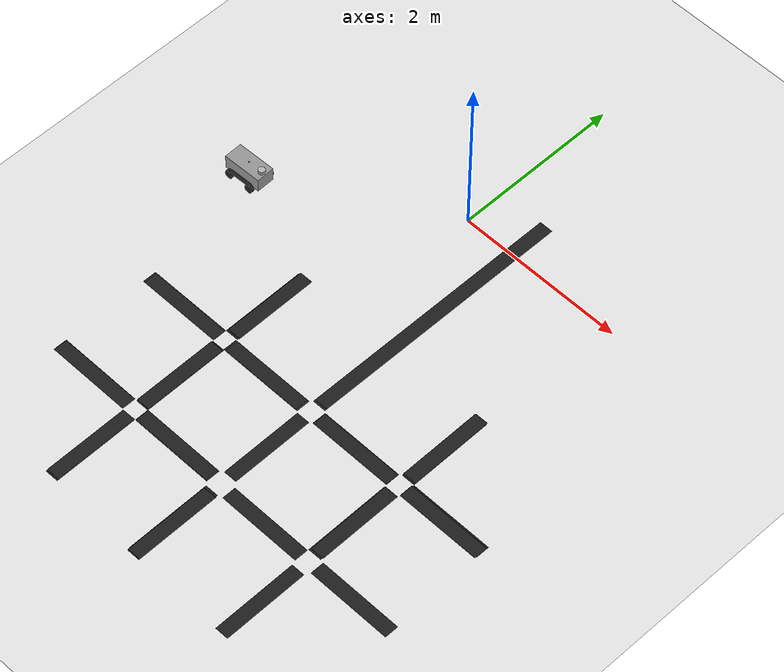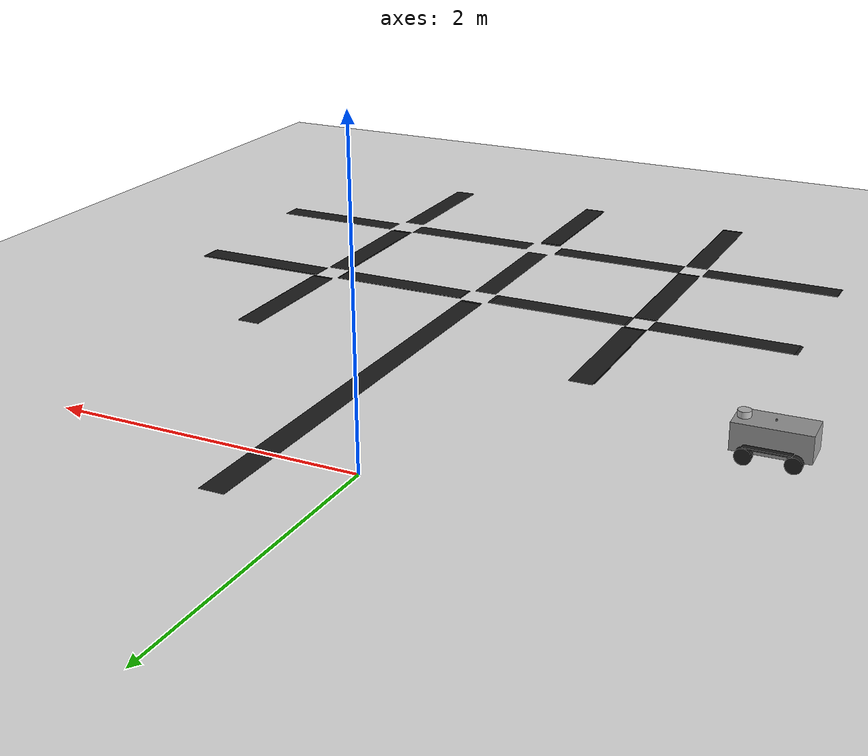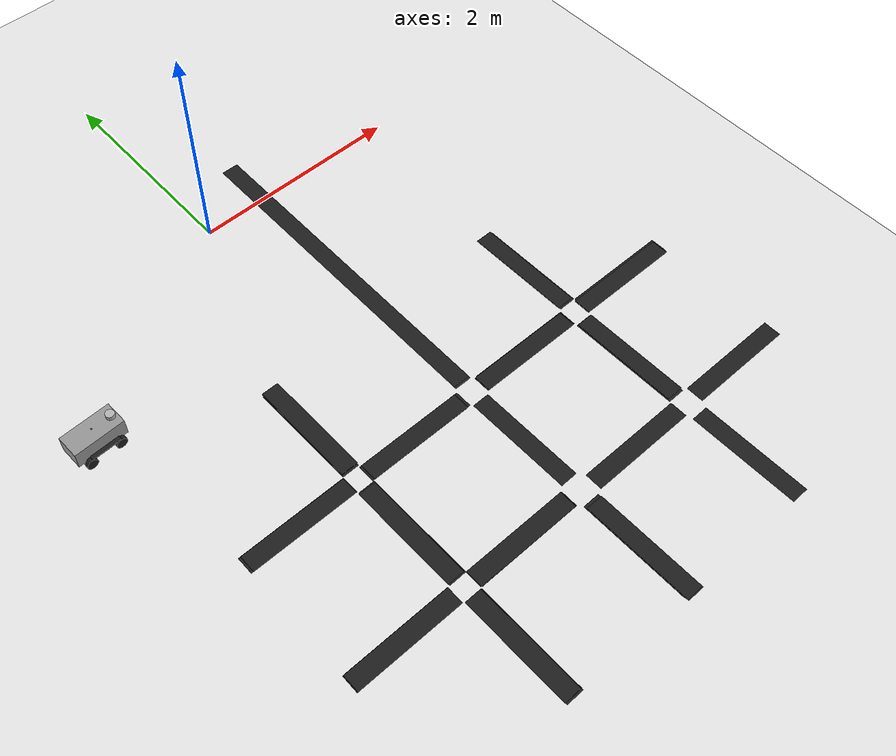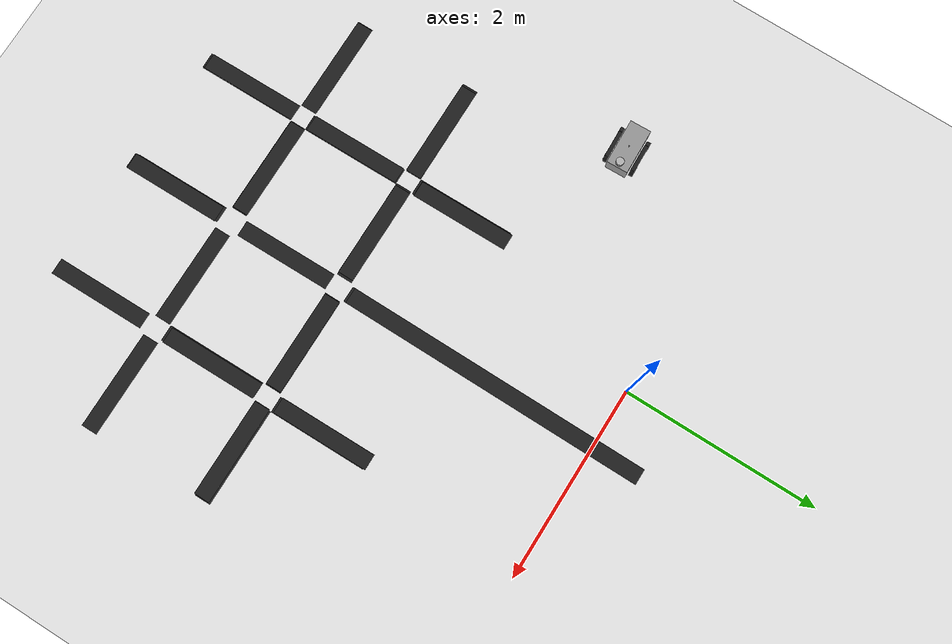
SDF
<sdf version="1.7">
 <world name="default">
  <light name="sun" type="directional">
   <pose>0 0 10 0 -0 0</pose>
   <diffuse>0.8 0.8 0.8 1</diffuse>
   <specular>0.2 0.2 0.2 1</specular>
   <attenuation>
    <range>1000</range>
    <constant>0.9</constant>
    <linear>0.01</linear>
    <quadratic>0.001</quadratic>
   </attenuation>
   <direction>-0.5 0.1 -0.9</direction>
   <spot><inner_angle>0</inner_angle><outer_angle>0</outer_angle><falloff>0</falloff></spot>
  </light>
  <model name="ground_plane">
   <static>1</static>
   <link name="link">
    <collision name="collision">
     <geometry><plane><normal>0 0 1</normal><size>100 100</size></plane></geometry>
     <surface>
      <contact><collide_bitmask>65535</collide_bitmask></contact>
      <friction><ode><mu>100</mu><mu2>50</mu2></ode></friction>
     </surface>
    </collision>
    <visual name="visual">
     <cast_shadows>0</cast_shadows>
     <geometry><plane><normal>0 0 1</normal><size>100 100</size></plane></geometry>
     <material>
      <script><uri>file://media/materials/scripts/gazebo.material</uri><name>Gazebo/White</name></script>
     </material>
    </visual>
   </link>
  </model>
  <model name="tankbot0">
   <pose>-1.96772 -1.17647 -0 -1e-06 3e-06 0.031298</pose>
   <frame name="tankbot::__model__" attached_to="tankbot::chassis">
    <pose relative_to="__model__">0 0 0 0 -0 0</pose>
   </frame>
   <link name="tankbot::chassis">
    <pose relative_to="tankbot::__model__">0 0 0.135 0 -0 0</pose>
    <inertial>
     <pose>0.0465 0 0 0 -0 0</pose>
     <mass>2</mass>
     <inertia>
      <ixx>0.0125927</ixx>
      <iyy>0.0408542</iyy>
      <izz>0.0438135</izz>
      <ixy>0</ixy>
      <ixz>0</ixz>
      <iyz>0</iyz>
     </inertia>
    </inertial>
    <collision name="collision"><geometry><box><size>0.465 0.216 0.17</size></box></geometry></collision>
    <visual name="visual">
     <geometry><box><size>0.465 0.216 0.17</size></box></geometry>
     <material>
      <script><uri>file://media/materials/scripts/gazebo.material</uri><name>Gazebo/Grey</name></script>
     </material>
    </visual>
   </link>
   <link name="tankbot::wheel_fl">
    <pose relative_to="tankbot::__model__">0.1395 0.142 0.05 -1.5708 -0.087266 0</pose>
    <inertial>
     <mass>0.25</mass>
     <inertia>
      <ixx>0.000189583</ixx>
      <iyy>0.000189583</iyy>
      <izz>0.0003125</izz>
      <ixy>0</ixy>
      <ixz>0</ixz>
      <iyz>0</iyz>
     </inertia>
    </inertial>
    <collision name="collision">
     <geometry><cylinder><radius>0.05</radius><length>0.04</length></cylinder></geometry>
    </collision>
    <visual name="tankbot::wheel_fl">
     <geometry><cylinder><radius>0.05</radius><length>0.04</length></cylinder></geometry>
     <material>
      <script><uri>file://media/materials/scripts/gazebo.material</uri><name>Gazebo/Black</name></script>
     </material>
    </visual>
   </link>
   <joint name="tankbot::wheel_fl_drive" type="revolute">
    <parent>tankbot::chassis</parent>
    <child>tankbot::wheel_fl</child>
    <axis>
     <xyz>0 0 1</xyz>
     <limit><lower>-1e+16</lower><upper>1e+16</upper></limit>
     <dynamics><spring_reference>0</spring_reference><spring_stiffness>0</spring_stiffness></dynamics>
    </axis>
   </joint>
   <link name="tankbot::chain_l_up">
    <pose relative_to="tankbot::__model__">0.0098 0.14 0.1 0 -0 0</pose>
    <gravity>0</gravity>
    <collision name="collision"><geometry><box><size>0.28 0.04 0.01</size></box></geometry></collision>
    <visual name="visual">
     <geometry><box><size>0.28 0.04 0.01</size></box></geometry>
     <material>
      <script><uri>file://media/materials/scripts/gazebo.material</uri><name>Gazebo/Black</name></script>
     </material>
    </visual>
    <inertial>
     <inertia><ixx>1</ixx><ixy>0</ixy><ixz>0</ixz><iyy>1</iyy><iyz>0</iyz><izz>1</izz></inertia>
     <mass>1</mass>
    </inertial>
   </link>
   <link name="tankbot::chain_r_up">
    <pose relative_to="tankbot::__model__">0.0098 -0.14 0.1 0 -0 0</pose>
    <gravity>0</gravity>
    <collision name="collision"><geometry><box><size>0.28 0.04 0.01</size></box></geometry></collision>
    <visual name="visual">
     <geometry><box><size>0.28 0.04 0.01</size></box></geometry>
     <material>
      <script><uri>file://media/materials/scripts/gazebo.material</uri><name>Gazebo/Black</name></script>
     </material>
    </visual>
    <inertial>
     <inertia><ixx>1</ixx><ixy>0</ixy><ixz>0</ixz><iyy>1</iyy><iyz>0</iyz><izz>1</izz></inertia>
     <mass>1</mass>
    </inertial>
   </link>
   <joint name="tankbot::chain_up_joint" type="revolute">
    <parent>tankbot::chassis</parent>
    <child>tankbot::chain_r_up</child>
   </joint>
   <joint name="tankbot::chain_up_2_joint" type="revolute">
    <parent>tankbot::chassis</parent>
    <child>tankbot::chain_l_up</child>
   </joint>
   <link name="tankbot::wheel_fr">
    <pose relative_to="tankbot::__model__">0.1395 -0.142 0.05 -1.5708 -0.087266 0</pose>
    <inertial>
     <mass>0.25</mass>
     <inertia>
      <ixx>0.000189583</ixx>
      <iyy>0.000189583</iyy>
      <izz>0.0003125</izz>
      <ixy>0</ixy>
      <ixz>0</ixz>
      <iyz>0</iyz>
     </inertia>
    </inertial>
    <collision name="collision">
     <geometry><cylinder><radius>0.05</radius><length>0.04</length></cylinder></geometry>
    </collision>
    <visual name="visual">
     <geometry><cylinder><radius>0.05</radius><length>0.04</length></cylinder></geometry>
     <material>
      <script><uri>file://media/materials/scripts/gazebo.material</uri><name>Gazebo/Black</name></script>
     </material>
    </visual>
   </link>
   <joint name="tankbot::wheel_fr_drive" type="revolute">
    <parent>tankbot::chassis</parent>
    <child>tankbot::wheel_fr</child>
    <axis>
     <xyz>0 0 1</xyz>
     <limit><lower>-1e+16</lower><upper>1e+16</upper></limit>
     <dynamics><spring_reference>0</spring_reference><spring_stiffness>0</spring_stiffness></dynamics>
    </axis>
   </joint>
   <link name="tankbot::wheel_rl">
    <pose relative_to="tankbot::__model__">-0.1395 0.142 0.05 -1.5708 0 0</pose>
    <inertial>
     <mass>0.25</mass>
     <inertia>
      <ixx>0.000189583</ixx>
      <iyy>0.000189583</iyy>
      <izz>0.0003125</izz>
      <ixy>0</ixy>
      <ixz>0</ixz>
      <iyz>0</iyz>
     </inertia>
    </inertial>
    <collision name="collision">
     <geometry><cylinder><radius>0</radius><length>0</length></cylinder></geometry>
    </collision>
    <visual name="visual">
     <geometry><cylinder><radius>0.05</radius><length>0.04</length></cylinder></geometry>
     <material>
      <script><uri>file://media/materials/scripts/gazebo.material</uri><name>Gazebo/Black</name></script>
     </material>
    </visual>
   </link>
   <joint name="tankbot::wheel_rl_drive" type="revolute">
    <parent>tankbot::chassis</parent>
    <child>tankbot::wheel_rl</child>
    <axis>
     <xyz>0 0 1</xyz>
     <limit><lower>-1e+16</lower><upper>1e+16</upper></limit>
     <dynamics><spring_reference>0</spring_reference><spring_stiffness>0</spring_stiffness></dynamics>
    </axis>
   </joint>
   <link name="tankbot::wheel_rr">
    <pose relative_to="tankbot::__model__">-0.1395 -0.142 0.05 -1.5708 0 0</pose>
    <inertial>
     <mass>0.25</mass>
     <inertia>
      <ixx>0.000189583</ixx>
      <iyy>0.000189583</iyy>
      <izz>0.0003125</izz>
      <ixy>0</ixy>
      <ixz>0</ixz>
      <iyz>0</iyz>
     </inertia>
    </inertial>
    <collision name="collision">
     <geometry><cylinder><radius>0.05</radius><length>0.04</length></cylinder></geometry>
    </collision>
    <visual name="visual">
     <geometry><cylinder><radius>0.05</radius><length>0.04</length></cylinder></geometry>
     <material>
      <script><uri>file://media/materials/scripts/gazebo.material</uri><name>Gazebo/Black</name></script>
     </material>
    </visual>
   </link>
   <joint name="tankbot::wheel_rr_drive" type="revolute">
    <parent>tankbot::chassis</parent>
    <child>tankbot::wheel_rr</child>
    <axis>
     <xyz>0 0 1</xyz>
     <limit><lower>-1e+16</lower><upper>1e+16</upper></limit>
     <dynamics><spring_reference>0</spring_reference><spring_stiffness>0</spring_stiffness></dynamics>
    </axis>
   </joint>
   <frame name="tankbot::ultrasonic_sensor::__model__" attached_to="tankbot::ultrasonic_sensor::link">
    <pose relative_to="tankbot::__model__">0.18 0 0.24 0 -0 0</pose>
   </frame>
   <link name="tankbot::ultrasonic_sensor::link">
    <inertial>
     <mass>0.1</mass>
     <inertia><ixx>1</ixx><ixy>0</ixy><ixz>0</ixz><iyy>1</iyy><iyz>0</iyz><izz>1</izz></inertia>
    </inertial>
    <visual name="visual">
     <geometry><cylinder><radius>0.04</radius><length>0.04</length></cylinder></geometry>
    </visual>
    <collision name="collision-base">
     <pose>0 0 -0.0145 0 -0 0</pose>
     <geometry><box><size>0.05 0.05 0.041</size></box></geometry>
    </collision>
    <collision name="collision-top">
     <pose>0 0 0.0205 0 -0 0</pose>
     <geometry><cylinder><radius>0.021</radius><length>0.029</length></cylinder></geometry>
    </collision>
    <sensor name="sonar" type="sonar">
     <pose>0.04 0 0 0 1.5 3.14</pose>
     <sonar><min>0</min><max>3</max><radius>0.3</radius></sonar>
     <plugin name="sonar" filename="libSonarPlugin.so"/>
     <always_on>1</always_on>
     <update_rate>30</update_rate>
     <visualize>1</visualize>
    </sensor>
    <pose relative_to="tankbot::ultrasonic_sensor::__model__">0 0 0 0 -0 0</pose>
   </link>
   <joint name="tankbot::sonar_joint" type="fixed">
    <child>tankbot::ultrasonic_sensor::link</child>
    <parent>tankbot::chassis</parent>
   </joint>
   <frame name="tankbot::camera_sensor::__model__" attached_to="tankbot::camera_sensor::link">
    <pose relative_to="tankbot::__model__">0.2 0 0.04 0 1.57 0</pose>
   </frame>
   <link name="tankbot::camera_sensor::link">
    <inertial>
     <mass>0.1</mass>
     <inertia><ixx>1</ixx><ixy>0</ixy><ixz>0</ixz><iyy>1</iyy><iyz>0</iyz><izz>1</izz></inertia>
    </inertial>
    <visual name="visual">
     <geometry><box><size>0.01 0.07 0.04</size></box></geometry>
     <material>
      <script><uri>file://media/materials/scripts/gazebo.material</uri><name>Gazebo/Red</name></script>
     </material>
    </visual>
    <collision name="collision">
     <pose>0 0 -0.0145 0 -0 0</pose>
     <geometry><box><size>0.01 0.07 0.04</size></box></geometry>
    </collision>
    <sensor name="camera" type="camera">
     <camera>
      <horizontal_fov>1.39626</horizontal_fov>
      <image><width>2</width><height>2</height></image>
      <clip><near>0.02</near><far>300</far></clip>
     </camera>
     <always_on>1</always_on>
     <update_rate>10</update_rate>
     <visualize>1</visualize>
     <plugin name="camera_controller" filename="libCameraPlugin.so"/>
    </sensor>
    <pose relative_to="tankbot::camera_sensor::__model__">0 0 0 0 -0 0</pose>
   </link>
   <frame name="tankbot::microphone_sensor::__model__" attached_to="tankbot::microphone_sensor::link">
    <pose relative_to="tankbot::__model__">0 0 0.23 0 -0 0</pose>
   </frame>
   <link name="tankbot::microphone_sensor::link">
    <inertial>
     <mass>0.1</mass>
     <inertia><ixx>1</ixx><ixy>0</ixy><ixz>0</ixz><iyy>1</iyy><iyz>0</iyz><izz>1</izz></inertia>
    </inertial>
    <visual name="visual">
     <geometry><box><size>0.01 0.01 0.01</size></box></geometry>
     <material>
      <script><uri>file://media/materials/scripts/gazebo.material</uri><name>Gazebo/Grey</name></script>
     </material>
    </visual>
    <collision name="collision"><geometry><box><size>0.01 0.01 0.01</size></box></geometry></collision>
    <pose relative_to="tankbot::microphone_sensor::__model__">0 0 0 0 -0 0</pose>
   </link>
   <plugin name="microphone_controller" filename="libmicrophone_control_plugin.so"/>
   <joint name="tankbot::camera_joint" type="fixed">
    <child>tankbot::camera_sensor::link</child>
    <parent>tankbot::chassis</parent>
   </joint>
   <plugin name="tankbot_control" filename="libtank_control_plugin.so"/>
   <plugin name="tankbot_control" filename="libtank_control_plugin.so"/>
  </model>
  <gravity>0 0 -9.8</gravity>
  <magnetic_field>6e-06 2.3e-05 -4.2e-05</magnetic_field>
  <atmosphere type="adiabatic"/>
  <physics type="ode">
   <max_step_size>0.001</max_step_size>
   <real_time_factor>1</real_time_factor>
   <real_time_update_rate>1000</real_time_update_rate>
  </physics>
  <scene><ambient>0.4 0.4 0.4 1</ambient><background>0.7 0.7 0.7 1</background><shadows>1</shadows></scene>
  <spherical_coordinates>
   <surface_model>EARTH_WGS84</surface_model>
   <latitude_deg>0</latitude_deg>
   <longitude_deg>0</longitude_deg>
   <elevation>0</elevation>
   <heading_deg>0</heading_deg>
  </spherical_coordinates>
  <model name="unit_box_clone_0_clone_clone_0">
   <link name="link">
    <inertial>
     <mass>1</mass>
     <inertia>
      <ixx>0.166667</ixx>
      <ixy>0</ixy>
      <ixz>0</ixz>
      <iyy>0.166667</iyy>
      <iyz>0</iyz>
      <izz>0.166667</izz>
     </inertia>
    </inertial>
    <visual name="visual">
     <geometry><box><size>1 0.160776 0.000937</size></box></geometry>
     <material>
      <script><name>Gazebo/Black</name><uri>file://media/materials/scripts/gazebo.material</uri></script>
      <shader type="pixel"><normal_map>__default__</normal_map></shader>
      <ambient>0 0 0 1</ambient>
      <diffuse>0 0 0 1</diffuse>
      <specular>0.1 0.1 0.1 1</specular>
      <emissive>0 0 0 1</emissive>
     </material>
    </visual>
    <collision name="collision">
     <geometry><box><size>1 0.160776 0.000937</size></box></geometry>
     <surface>
      <friction>
       <ode><mu>1</mu><mu2>1</mu2><fdir1>0 0 0</fdir1><slip1>0</slip1><slip2>0</slip2></ode>
       <torsional>
        <coefficient>1</coefficient>
        <patch_radius>0</patch_radius>
        <surface_radius>0</surface_radius>
        <use_patch_radius>1</use_patch_radius>
        <ode><slip>0</slip></ode>
       </torsional>
      </friction>
      <bounce><restitution_coefficient>0</restitution_coefficient><threshold>1e+06</threshold></bounce>
      <contact>
       <collide_without_contact>0</collide_without_contact>
       <collide_without_contact_bitmask>1</collide_without_contact_bitmask>
       <collide_bitmask>1</collide_bitmask>
       <ode>
        <soft_cfm>0</soft_cfm>
        <soft_erp>0.2</soft_erp>
        <kp>1e+13</kp>
        <kd>1</kd>
        <max_vel>0.01</max_vel>
        <min_depth>0</min_depth>
       </ode>
       <bullet>
        <split_impulse>1</split_impulse>
        <split_impulse_penetration_threshold>-0.01</split_impulse_penetration_threshold>
        <soft_cfm>0</soft_cfm>
        <soft_erp>0.2</soft_erp>
        <kp>1e+13</kp>
        <kd>1</kd>
       </bullet>
      </contact>
     </surface>
    </collision>
   </link>
   <static>0</static>
   <pose>-0.008686 -2.79023 0.002211 -2e-06 -1.2e-05 -0.000646</pose>
  </model>
  <model name="unit_box_clone_0_clone_clone_clone_clone_clone_clone_clone_0_clone">
   <link name="link">
    <inertial>
     <mass>1</mass>
     <inertia>
      <ixx>0.166667</ixx>
      <ixy>0</ixy>
      <ixz>0</ixz>
      <iyy>0.166667</iyy>
      <iyz>0</iyz>
      <izz>0.166667</izz>
     </inertia>
    </inertial>
    <visual name="visual">
     <geometry><box><size>3.16167 0.161571 0.000937</size></box></geometry>
     <material>
      <script><name>Gazebo/Black</name><uri>file://media/materials/scripts/gazebo.material</uri></script>
      <shader type="pixel"><normal_map>__default__</normal_map></shader>
      <ambient>0 0 0 1</ambient>
      <diffuse>0 0 0 1</diffuse>
      <specular>0.1 0.1 0.1 1</specular>
      <emissive>0 0 0 1</emissive>
     </material>
    </visual>
    <collision name="collision">
     <geometry><box><size>3.16167 0.161571 0.000937</size></box></geometry>
     <surface>
      <friction>
       <ode><mu>1</mu><mu2>1</mu2><fdir1>0 0 0</fdir1><slip1>0</slip1><slip2>0</slip2></ode>
       <torsional>
        <coefficient>1</coefficient>
        <patch_radius>0</patch_radius>
        <surface_radius>0</surface_radius>
        <use_patch_radius>1</use_patch_radius>
        <ode><slip>0</slip></ode>
       </torsional>
      </friction>
      <bounce><restitution_coefficient>0</restitution_coefficient><threshold>1e+06</threshold></bounce>
      <contact>
       <collide_without_contact>0</collide_without_contact>
       <collide_without_contact_bitmask>1</collide_without_contact_bitmask>
       <collide_bitmask>1</collide_bitmask>
       <ode>
        <soft_cfm>0</soft_cfm>
        <soft_erp>0.2</soft_erp>
        <kp>1e+13</kp>
        <kd>1</kd>
        <max_vel>0.01</max_vel>
        <min_depth>0</min_depth>
       </ode>
       <bullet>
        <split_impulse>1</split_impulse>
        <split_impulse_penetration_threshold>-0.01</split_impulse_penetration_threshold>
        <soft_cfm>0</soft_cfm>
        <soft_erp>0.2</soft_erp>
        <kp>1e+13</kp>
        <kd>1</kd>
       </bullet>
      </contact>
     </surface>
    </collision>
   </link>
   <static>0</static>
   <pose>0.602322 -1.09658 -4e-05 6e-06 -0.000322 -1.57395</pose>
  </model>
  <model name="unit_box_clone_0_clone_clone_0_clone">
   <link name="link">
    <inertial>
     <mass>1</mass>
     <inertia>
      <ixx>0.166667</ixx>
      <ixy>0</ixy>
      <ixz>0</ixz>
      <iyy>0.166667</iyy>
      <iyz>0</iyz>
      <izz>0.166667</izz>
     </inertia>
    </inertial>
    <visual name="visual">
     <geometry><box><size>1 0.160776 0.000937</size></box></geometry>
     <material>
      <script><name>Gazebo/Black</name><uri>file://media/materials/scripts/gazebo.material</uri></script>
      <shader type="pixel"><normal_map>__default__</normal_map></shader>
      <ambient>0 0 0 1</ambient>
      <diffuse>0 0 0 1</diffuse>
      <specular>0.1 0.1 0.1 1</specular>
      <emissive>0 0 0 1</emissive>
     </material>
    </visual>
    <collision name="collision">
     <geometry><box><size>1 0.160776 0.000937</size></box></geometry>
     <surface>
      <friction>
       <ode><mu>1</mu><mu2>1</mu2><fdir1>0 0 0</fdir1><slip1>0</slip1><slip2>0</slip2></ode>
       <torsional>
        <coefficient>1</coefficient>
        <patch_radius>0</patch_radius>
        <surface_radius>0</surface_radius>
        <use_patch_radius>1</use_patch_radius>
        <ode><slip>0</slip></ode>
       </torsional>
      </friction>
      <bounce><restitution_coefficient>0</restitution_coefficient><threshold>1e+06</threshold></bounce>
      <contact>
       <collide_without_contact>0</collide_without_contact>
       <collide_without_contact_bitmask>1</collide_without_contact_bitmask>
       <collide_bitmask>1</collide_bitmask>
       <ode>
        <soft_cfm>0</soft_cfm>
        <soft_erp>0.2</soft_erp>
        <kp>1e+13</kp>
        <kd>1</kd>
        <max_vel>0.01</max_vel>
        <min_depth>0</min_depth>
       </ode>
       <bullet>
        <split_impulse>1</split_impulse>
        <split_impulse_penetration_threshold>-0.01</split_impulse_penetration_threshold>
        <soft_cfm>0</soft_cfm>
        <soft_erp>0.2</soft_erp>
        <kp>1e+13</kp>
        <kd>1</kd>
       </bullet>
      </contact>
     </surface>
    </collision>
   </link>
   <static>0</static>
   <pose>1.21707 -2.77877 0.001392 -5e-06 2.8e-05 -3.8e-05</pose>
  </model>
  <model name="unit_box_clone_0_clone_clone_0_clone_clone">
   <link name="link">
    <inertial>
     <mass>1</mass>
     <inertia>
      <ixx>0.166667</ixx>
      <ixy>0</ixy>
      <ixz>0</ixz>
      <iyy>0.166667</iyy>
      <iyz>0</iyz>
      <izz>0.166667</izz>
     </inertia>
    </inertial>
    <visual name="visual">
     <geometry><box><size>0.983697 0.160776 0.000937</size></box></geometry>
     <material>
      <script><name>Gazebo/Black</name><uri>file://media/materials/scripts/gazebo.material</uri></script>
      <shader type="pixel"><normal_map>__default__</normal_map></shader>
      <ambient>0 0 0 1</ambient>
      <diffuse>0 0 0 1</diffuse>
      <specular>0.1 0.1 0.1 1</specular>
      <emissive>0 0 0 1</emissive>
     </material>
    </visual>
    <collision name="collision">
     <geometry><box><size>0.983697 0.160776 0.000937</size></box></geometry>
     <surface>
      <friction>
       <ode><mu>1</mu><mu2>1</mu2><fdir1>0 0 0</fdir1><slip1>0</slip1><slip2>0</slip2></ode>
       <torsional>
        <coefficient>1</coefficient>
        <patch_radius>0</patch_radius>
        <surface_radius>0</surface_radius>
        <use_patch_radius>1</use_patch_radius>
        <ode><slip>0</slip></ode>
       </torsional>
      </friction>
      <bounce><restitution_coefficient>0</restitution_coefficient><threshold>1e+06</threshold></bounce>
      <contact>
       <collide_without_contact>0</collide_without_contact>
       <collide_without_contact_bitmask>1</collide_without_contact_bitmask>
       <collide_bitmask>1</collide_bitmask>
       <ode>
        <soft_cfm>0</soft_cfm>
        <soft_erp>0.2</soft_erp>
        <kp>1e+13</kp>
        <kd>1</kd>
        <max_vel>0.01</max_vel>
        <min_depth>0</min_depth>
       </ode>
       <bullet>
        <split_impulse>1</split_impulse>
        <split_impulse_penetration_threshold>-0.01</split_impulse_penetration_threshold>
        <soft_cfm>0</soft_cfm>
        <soft_erp>0.2</soft_erp>
        <kp>1e+13</kp>
        <kd>1</kd>
       </bullet>
      </contact>
     </surface>
    </collision>
   </link>
   <static>0</static>
   <pose>0.595049 -3.38053 0.000464 0 -9e-06 -1.56217</pose>
  </model>
  <model name="unit_box_clone_0_clone_clone_0_clone_clone_clone">
   <link name="link">
    <inertial>
     <mass>1</mass>
     <inertia>
      <ixx>0.166667</ixx>
      <ixy>0</ixy>
      <ixz>0</ixz>
      <iyy>0.166667</iyy>
      <iyz>0</iyz>
      <izz>0.166667</izz>
     </inertia>
    </inertial>
    <visual name="visual">
     <geometry><box><size>1 0.160776 0.000937</size></box></geometry>
     <material>
      <script><name>Gazebo/Black</name><uri>file://media/materials/scripts/gazebo.material</uri></script>
      <shader type="pixel"><normal_map>__default__</normal_map></shader>
      <ambient>0 0 0 1</ambient>
      <diffuse>0 0 0 1</diffuse>
      <specular>0.1 0.1 0.1 1</specular>
      <emissive>0 0 0 1</emissive>
     </material>
    </visual>
    <collision name="collision">
     <geometry><box><size>1 0.160776 0.000937</size></box></geometry>
     <surface>
      <friction>
       <ode><mu>1</mu><mu2>1</mu2><fdir1>0 0 0</fdir1><slip1>0</slip1><slip2>0</slip2></ode>
       <torsional>
        <coefficient>1</coefficient>
        <patch_radius>0</patch_radius>
        <surface_radius>0</surface_radius>
        <use_patch_radius>1</use_patch_radius>
        <ode><slip>0</slip></ode>
       </torsional>
      </friction>
      <bounce><restitution_coefficient>0</restitution_coefficient><threshold>1e+06</threshold></bounce>
      <contact>
       <collide_without_contact>0</collide_without_contact>
       <collide_without_contact_bitmask>1</collide_without_contact_bitmask>
       <collide_bitmask>1</collide_bitmask>
       <ode>
        <soft_cfm>0</soft_cfm>
        <soft_erp>0.2</soft_erp>
        <kp>1e+13</kp>
        <kd>1</kd>
        <max_vel>0.01</max_vel>
        <min_depth>0</min_depth>
       </ode>
       <bullet>
        <split_impulse>1</split_impulse>
        <split_impulse_penetration_threshold>-0.01</split_impulse_penetration_threshold>
        <soft_cfm>0</soft_cfm>
        <soft_erp>0.2</soft_erp>
        <kp>1e+13</kp>
        <kd>1</kd>
       </bullet>
      </contact>
     </surface>
    </collision>
   </link>
   <static>0</static>
   <pose>1.82845 -4.64722 0.000469 0 0 -1.56225</pose>
  </model>
  <model name="unit_box_clone_0_clone_clone_0_clone_clone_0">
   <link name="link">
    <inertial>
     <mass>1</mass>
     <inertia>
      <ixx>0.166667</ixx>
      <ixy>0</ixy>
      <ixz>0</ixz>
      <iyy>0.166667</iyy>
      <iyz>0</iyz>
      <izz>0.166667</izz>
     </inertia>
    </inertial>
    <visual name="visual">
     <geometry><box><size>1 0.160776 0.000937</size></box></geometry>
     <material>
      <script><name>Gazebo/Black</name><uri>file://media/materials/scripts/gazebo.material</uri></script>
      <shader type="pixel"><normal_map>__default__</normal_map></shader>
      <ambient>0 0 0 1</ambient>
      <diffuse>0 0 0 1</diffuse>
      <specular>0.1 0.1 0.1 1</specular>
      <emissive>0 0 0 1</emissive>
     </material>
    </visual>
    <collision name="collision">
     <geometry><box><size>1 0.160776 0.000937</size></box></geometry>
     <surface>
      <friction>
       <ode><mu>1</mu><mu2>1</mu2><fdir1>0 0 0</fdir1><slip1>0</slip1><slip2>0</slip2></ode>
       <torsional>
        <coefficient>1</coefficient>
        <patch_radius>0</patch_radius>
        <surface_radius>0</surface_radius>
        <use_patch_radius>1</use_patch_radius>
        <ode><slip>0</slip></ode>
       </torsional>
      </friction>
      <bounce><restitution_coefficient>0</restitution_coefficient><threshold>1e+06</threshold></bounce>
      <contact>
       <collide_without_contact>0</collide_without_contact>
       <collide_without_contact_bitmask>1</collide_without_contact_bitmask>
       <collide_bitmask>1</collide_bitmask>
       <ode>
        <soft_cfm>0</soft_cfm>
        <soft_erp>0.2</soft_erp>
        <kp>1e+13</kp>
        <kd>1</kd>
        <max_vel>0.01</max_vel>
        <min_depth>0</min_depth>
       </ode>
       <bullet>
        <split_impulse>1</split_impulse>
        <split_impulse_penetration_threshold>-0.01</split_impulse_penetration_threshold>
        <soft_cfm>0</soft_cfm>
        <soft_erp>0.2</soft_erp>
        <kp>1e+13</kp>
        <kd>1</kd>
       </bullet>
      </contact>
     </surface>
    </collision>
   </link>
   <static>0</static>
   <pose>2.40671 -2.76247 0.001279 2e-06 -1.2e-05 0.000249</pose>
  </model>
  <model name="unit_box_clone_0_clone_clone_0_clone_clone_clone_0">
   <link name="link">
    <inertial>
     <mass>1</mass>
     <inertia>
      <ixx>0.166667</ixx>
      <ixy>0</ixy>
      <ixz>0</ixz>
      <iyy>0.166667</iyy>
      <iyz>0</iyz>
      <izz>0.166667</izz>
     </inertia>
    </inertial>
    <visual name="visual">
     <geometry><box><size>1 0.160776 0.000937</size></box></geometry>
     <material>
      <script><name>Gazebo/Black</name><uri>file://media/materials/scripts/gazebo.material</uri></script>
      <shader type="pixel"><normal_map>__default__</normal_map></shader>
      <ambient>0 0 0 1</ambient>
      <diffuse>0 0 0 1</diffuse>
      <specular>0.1 0.1 0.1 1</specular>
      <emissive>0 0 0 1</emissive>
     </material>
    </visual>
    <collision name="collision">
     <geometry><box><size>1 0.160776 0.000937</size></box></geometry>
     <surface>
      <friction>
       <ode><mu>1</mu><mu2>1</mu2><fdir1>0 0 0</fdir1><slip1>0</slip1><slip2>0</slip2></ode>
       <torsional>
        <coefficient>1</coefficient>
        <patch_radius>0</patch_radius>
        <surface_radius>0</surface_radius>
        <use_patch_radius>1</use_patch_radius>
        <ode><slip>0</slip></ode>
       </torsional>
      </friction>
      <bounce><restitution_coefficient>0</restitution_coefficient><threshold>1e+06</threshold></bounce>
      <contact>
       <collide_without_contact>0</collide_without_contact>
       <collide_without_contact_bitmask>1</collide_without_contact_bitmask>
       <collide_bitmask>1</collide_bitmask>
       <ode>
        <soft_cfm>0</soft_cfm>
        <soft_erp>0.2</soft_erp>
        <kp>1e+13</kp>
        <kd>1</kd>
        <max_vel>0.01</max_vel>
        <min_depth>0</min_depth>
       </ode>
       <bullet>
        <split_impulse>1</split_impulse>
        <split_impulse_penetration_threshold>-0.01</split_impulse_penetration_threshold>
        <soft_cfm>0</soft_cfm>
        <soft_erp>0.2</soft_erp>
        <kp>1e+13</kp>
        <kd>1</kd>
       </bullet>
      </contact>
     </surface>
    </collision>
   </link>
   <static>0</static>
   <pose>1.81587 -2.15805 0.00219 1e-06 -6.2e-05 -1.56218</pose>
  </model>
  <model name="unit_box_clone_0_clone_clone_0_clone_0">
   <link name="link">
    <inertial>
     <mass>1</mass>
     <inertia>
      <ixx>0.166667</ixx>
      <ixy>0</ixy>
      <ixz>0</ixz>
      <iyy>0.166667</iyy>
      <iyz>0</iyz>
      <izz>0.166667</izz>
     </inertia>
    </inertial>
    <visual name="visual">
     <geometry><box><size>1 0.160776 0.000937</size></box></geometry>
     <material>
      <script><name>Gazebo/Black</name><uri>file://media/materials/scripts/gazebo.material</uri></script>
      <shader type="pixel"><normal_map>__default__</normal_map></shader>
      <ambient>0 0 0 1</ambient>
      <diffuse>0 0 0 1</diffuse>
      <specular>0.1 0.1 0.1 1</specular>
      <emissive>0 0 0 1</emissive>
     </material>
    </visual>
    <collision name="collision">
     <geometry><box><size>1 0.160776 0.000937</size></box></geometry>
     <surface>
      <friction>
       <ode><mu>1</mu><mu2>1</mu2><fdir1>0 0 0</fdir1><slip1>0</slip1><slip2>0</slip2></ode>
       <torsional>
        <coefficient>1</coefficient>
        <patch_radius>0</patch_radius>
        <surface_radius>0</surface_radius>
        <use_patch_radius>1</use_patch_radius>
        <ode><slip>0</slip></ode>
       </torsional>
      </friction>
      <bounce><restitution_coefficient>0</restitution_coefficient><threshold>1e+06</threshold></bounce>
      <contact>
       <collide_without_contact>0</collide_without_contact>
       <collide_without_contact_bitmask>1</collide_without_contact_bitmask>
       <collide_bitmask>1</collide_bitmask>
       <ode>
        <soft_cfm>0</soft_cfm>
        <soft_erp>0.2</soft_erp>
        <kp>1e+13</kp>
        <kd>1</kd>
        <max_vel>0.01</max_vel>
        <min_depth>0</min_depth>
       </ode>
       <bullet>
        <split_impulse>1</split_impulse>
        <split_impulse_penetration_threshold>-0.01</split_impulse_penetration_threshold>
        <soft_cfm>0</soft_cfm>
        <soft_erp>0.2</soft_erp>
        <kp>1e+13</kp>
        <kd>1</kd>
       </bullet>
      </contact>
     </surface>
    </collision>
   </link>
   <static>0</static>
   <pose>-1.20913 -2.78457 0.00188 -1.4e-05 0.000134 -0.000392</pose>
  </model>
  <model name="unit_box_clone_0_clone_clone_0_clone_clone_clone_1">
   <link name="link">
    <inertial>
     <mass>1</mass>
     <inertia>
      <ixx>0.166667</ixx>
      <ixy>0</ixy>
      <ixz>0</ixz>
      <iyy>0.166667</iyy>
      <iyz>0</iyz>
      <izz>0.166667</izz>
     </inertia>
    </inertial>
    <visual name="visual">
     <geometry><box><size>1 0.160776 0.000937</size></box></geometry>
     <material>
      <script><name>Gazebo/Black</name><uri>file://media/materials/scripts/gazebo.material</uri></script>
      <shader type="pixel"><normal_map>__default__</normal_map></shader>
      <ambient>0 0 0 1</ambient>
      <diffuse>0 0 0 1</diffuse>
      <specular>0.1 0.1 0.1 1</specular>
      <emissive>0 0 0 1</emissive>
     </material>
    </visual>
    <collision name="collision">
     <geometry><box><size>1 0.160776 0.000937</size></box></geometry>
     <surface>
      <friction>
       <ode><mu>1</mu><mu2>1</mu2><fdir1>0 0 0</fdir1><slip1>0</slip1><slip2>0</slip2></ode>
       <torsional>
        <coefficient>1</coefficient>
        <patch_radius>0</patch_radius>
        <surface_radius>0</surface_radius>
        <use_patch_radius>1</use_patch_radius>
        <ode><slip>0</slip></ode>
       </torsional>
      </friction>
      <bounce><restitution_coefficient>0</restitution_coefficient><threshold>1e+06</threshold></bounce>
      <contact>
       <collide_without_contact>0</collide_without_contact>
       <collide_without_contact_bitmask>1</collide_without_contact_bitmask>
       <collide_bitmask>1</collide_bitmask>
       <ode>
        <soft_cfm>0</soft_cfm>
        <soft_erp>0.2</soft_erp>
        <kp>1e+13</kp>
        <kd>1</kd>
        <max_vel>0.01</max_vel>
        <min_depth>0</min_depth>
       </ode>
       <bullet>
        <split_impulse>1</split_impulse>
        <split_impulse_penetration_threshold>-0.01</split_impulse_penetration_threshold>
        <soft_cfm>0</soft_cfm>
        <soft_erp>0.2</soft_erp>
        <kp>1e+13</kp>
        <kd>1</kd>
       </bullet>
      </contact>
     </surface>
    </collision>
   </link>
   <static>0</static>
   <pose>-0.613913 -4.59039 0.000463 -1e-06 1.1e-05 -1.562</pose>
  </model>
  <model name="unit_box_clone_0_clone_clone_0_clone_clone_clone_0_clone">
   <link name="link">
    <inertial>
     <mass>1</mass>
     <inertia>
      <ixx>0.166667</ixx>
      <ixy>0</ixy>
      <ixz>0</ixz>
      <iyy>0.166667</iyy>
      <iyz>0</iyz>
      <izz>0.166667</izz>
     </inertia>
    </inertial>
    <visual name="visual">
     <geometry><box><size>1 0.160776 0.000937</size></box></geometry>
     <material>
      <script><name>Gazebo/Black</name><uri>file://media/materials/scripts/gazebo.material</uri></script>
      <shader type="pixel"><normal_map>__default__</normal_map></shader>
      <ambient>0 0 0 1</ambient>
      <diffuse>0 0 0 1</diffuse>
      <specular>0.1 0.1 0.1 1</specular>
      <emissive>0 0 0 1</emissive>
     </material>
    </visual>
    <collision name="collision">
     <geometry><box><size>1 0.160776 0.000937</size></box></geometry>
     <surface>
      <friction>
       <ode><mu>1</mu><mu2>1</mu2><fdir1>0 0 0</fdir1><slip1>0</slip1><slip2>0</slip2></ode>
       <torsional>
        <coefficient>1</coefficient>
        <patch_radius>0</patch_radius>
        <surface_radius>0</surface_radius>
        <use_patch_radius>1</use_patch_radius>
        <ode><slip>0</slip></ode>
       </torsional>
      </friction>
      <bounce><restitution_coefficient>0</restitution_coefficient><threshold>1e+06</threshold></bounce>
      <contact>
       <collide_without_contact>0</collide_without_contact>
       <collide_without_contact_bitmask>1</collide_without_contact_bitmask>
       <collide_bitmask>1</collide_bitmask>
       <ode>
        <soft_cfm>0</soft_cfm>
        <soft_erp>0.2</soft_erp>
        <kp>1e+13</kp>
        <kd>1</kd>
        <max_vel>0.01</max_vel>
        <min_depth>0</min_depth>
       </ode>
       <bullet>
        <split_impulse>1</split_impulse>
        <split_impulse_penetration_threshold>-0.01</split_impulse_penetration_threshold>
        <soft_cfm>0</soft_cfm>
        <soft_erp>0.2</soft_erp>
        <kp>1e+13</kp>
        <kd>1</kd>
       </bullet>
      </contact>
     </surface>
    </collision>
   </link>
   <static>0</static>
   <pose>-0.619432 -2.17031 0.002209 -3e-06 2.2e-05 -1.5622</pose>
  </model>
  <model name="unit_box_clone_0_clone_clone_0_clone_1">
   <link name="link">
    <inertial>
     <mass>1</mass>
     <inertia>
      <ixx>0.166667</ixx>
      <ixy>0</ixy>
      <ixz>0</ixz>
      <iyy>0.166667</iyy>
      <iyz>0</iyz>
      <izz>0.166667</izz>
     </inertia>
    </inertial>
    <visual name="visual">
     <geometry><box><size>1 0.160776 0.000937</size></box></geometry>
     <material>
      <script><name>Gazebo/Black</name><uri>file://media/materials/scripts/gazebo.material</uri></script>
      <shader type="pixel"><normal_map>__default__</normal_map></shader>
      <ambient>0 0 0 1</ambient>
      <diffuse>0 0 0 1</diffuse>
      <specular>0.1 0.1 0.1 1</specular>
      <emissive>0 0 0 1</emissive>
     </material>
    </visual>
    <collision name="collision">
     <geometry><box><size>1 0.160776 0.000937</size></box></geometry>
     <surface>
      <friction>
       <ode><mu>1</mu><mu2>1</mu2><fdir1>0 0 0</fdir1><slip1>0</slip1><slip2>0</slip2></ode>
       <torsional>
        <coefficient>1</coefficient>
        <patch_radius>0</patch_radius>
        <surface_radius>0</surface_radius>
        <use_patch_radius>1</use_patch_radius>
        <ode><slip>0</slip></ode>
       </torsional>
      </friction>
      <bounce><restitution_coefficient>0</restitution_coefficient><threshold>1e+06</threshold></bounce>
      <contact>
       <collide_without_contact>0</collide_without_contact>
       <collide_without_contact_bitmask>1</collide_without_contact_bitmask>
       <collide_bitmask>1</collide_bitmask>
       <ode>
        <soft_cfm>0</soft_cfm>
        <soft_erp>0.2</soft_erp>
        <kp>1e+13</kp>
        <kd>1</kd>
        <max_vel>0.01</max_vel>
        <min_depth>0</min_depth>
       </ode>
       <bullet>
        <split_impulse>1</split_impulse>
        <split_impulse_penetration_threshold>-0.01</split_impulse_penetration_threshold>
        <soft_cfm>0</soft_cfm>
        <soft_erp>0.2</soft_erp>
        <kp>1e+13</kp>
        <kd>1</kd>
       </bullet>
      </contact>
     </surface>
    </collision>
   </link>
   <static>0</static>
   <pose>-0.021603 -3.98781 0.000431 1.6e-05 -6.2e-05 0.000146</pose>
  </model>
  <model name="unit_box_clone_0_clone_clone_0_clone_clone_1">
   <link name="link">
    <inertial>
     <mass>1</mass>
     <inertia>
      <ixx>0.166667</ixx>
      <ixy>0</ixy>
      <ixz>0</ixz>
      <iyy>0.166667</iyy>
      <iyz>0</iyz>
      <izz>0.166667</izz>
     </inertia>
    </inertial>
    <visual name="visual">
     <geometry><box><size>1 0.160776 0.000937</size></box></geometry>
     <material>
      <script><name>Gazebo/Black</name><uri>file://media/materials/scripts/gazebo.material</uri></script>
      <shader type="pixel"><normal_map>__default__</normal_map></shader>
      <ambient>0 0 0 1</ambient>
      <diffuse>0 0 0 1</diffuse>
      <specular>0.1 0.1 0.1 1</specular>
      <emissive>0 0 0 1</emissive>
     </material>
    </visual>
    <collision name="collision">
     <geometry><box><size>1 0.160776 0.000937</size></box></geometry>
     <surface>
      <friction>
       <ode><mu>1</mu><mu2>1</mu2><fdir1>0 0 0</fdir1><slip1>0</slip1><slip2>0</slip2></ode>
       <torsional>
        <coefficient>1</coefficient>
        <patch_radius>0</patch_radius>
        <surface_radius>0</surface_radius>
        <use_patch_radius>1</use_patch_radius>
        <ode><slip>0</slip></ode>
       </torsional>
      </friction>
      <bounce><restitution_coefficient>0</restitution_coefficient><threshold>1e+06</threshold></bounce>
      <contact>
       <collide_without_contact>0</collide_without_contact>
       <collide_without_contact_bitmask>1</collide_without_contact_bitmask>
       <collide_bitmask>1</collide_bitmask>
       <ode>
        <soft_cfm>0</soft_cfm>
        <soft_erp>0.2</soft_erp>
        <kp>1e+13</kp>
        <kd>1</kd>
        <max_vel>0.01</max_vel>
        <min_depth>0</min_depth>
       </ode>
       <bullet>
        <split_impulse>1</split_impulse>
        <split_impulse_penetration_threshold>-0.01</split_impulse_penetration_threshold>
        <soft_cfm>0</soft_cfm>
        <soft_erp>0.2</soft_erp>
        <kp>1e+13</kp>
        <kd>1</kd>
       </bullet>
      </contact>
     </surface>
    </collision>
   </link>
   <static>0</static>
   <pose>1.22708 -4.01051 0.000466 -0 -5e-06 -3.7e-05</pose>
  </model>
  <model name="unit_box_clone_0_clone_clone_0_clone_clone_0_clone">
   <link name="link">
    <inertial>
     <mass>1</mass>
     <inertia>
      <ixx>0.166667</ixx>
      <ixy>0</ixy>
      <ixz>0</ixz>
      <iyy>0.166667</iyy>
      <iyz>0</iyz>
      <izz>0.166667</izz>
     </inertia>
    </inertial>
    <visual name="visual">
     <geometry><box><size>1 0.160776 0.000937</size></box></geometry>
     <material>
      <script><name>Gazebo/Black</name><uri>file://media/materials/scripts/gazebo.material</uri></script>
      <shader type="pixel"><normal_map>__default__</normal_map></shader>
      <ambient>0 0 0 1</ambient>
      <diffuse>0 0 0 1</diffuse>
      <specular>0.1 0.1 0.1 1</specular>
      <emissive>0 0 0 1</emissive>
     </material>
    </visual>
    <collision name="collision">
     <geometry><box><size>1 0.160776 0.000937</size></box></geometry>
     <surface>
      <friction>
       <ode><mu>1</mu><mu2>1</mu2><fdir1>0 0 0</fdir1><slip1>0</slip1><slip2>0</slip2></ode>
       <torsional>
        <coefficient>1</coefficient>
        <patch_radius>0</patch_radius>
        <surface_radius>0</surface_radius>
        <use_patch_radius>1</use_patch_radius>
        <ode><slip>0</slip></ode>
       </torsional>
      </friction>
      <bounce><restitution_coefficient>0</restitution_coefficient><threshold>1e+06</threshold></bounce>
      <contact>
       <collide_without_contact>0</collide_without_contact>
       <collide_without_contact_bitmask>1</collide_without_contact_bitmask>
       <collide_bitmask>1</collide_bitmask>
       <ode>
        <soft_cfm>0</soft_cfm>
        <soft_erp>0.2</soft_erp>
        <kp>1e+13</kp>
        <kd>1</kd>
        <max_vel>0.01</max_vel>
        <min_depth>0</min_depth>
       </ode>
       <bullet>
        <split_impulse>1</split_impulse>
        <split_impulse_penetration_threshold>-0.01</split_impulse_penetration_threshold>
        <soft_cfm>0</soft_cfm>
        <soft_erp>0.2</soft_erp>
        <kp>1e+13</kp>
        <kd>1</kd>
       </bullet>
      </contact>
     </surface>
    </collision>
   </link>
   <static>0</static>
   <pose>2.43435 -4.00376 0.000469 0 -0 0.00022</pose>
  </model>
  <model name="unit_box_clone_0_clone_clone_0_clone_clone_clone_2">
   <link name="link">
    <inertial>
     <mass>1</mass>
     <inertia>
      <ixx>0.166667</ixx>
      <ixy>0</ixy>
      <ixz>0</ixz>
      <iyy>0.166667</iyy>
      <iyz>0</iyz>
      <izz>0.166667</izz>
     </inertia>
    </inertial>
    <visual name="visual">
     <geometry><box><size>1 0.160776 0.000937</size></box></geometry>
     <material>
      <script><name>Gazebo/Black</name><uri>file://media/materials/scripts/gazebo.material</uri></script>
      <shader type="pixel"><normal_map>__default__</normal_map></shader>
      <ambient>0 0 0 1</ambient>
      <diffuse>0 0 0 1</diffuse>
      <specular>0.1 0.1 0.1 1</specular>
      <emissive>0 0 0 1</emissive>
     </material>
    </visual>
    <collision name="collision">
     <geometry><box><size>1 0.160776 0.000937</size></box></geometry>
     <surface>
      <friction>
       <ode><mu>1</mu><mu2>1</mu2><fdir1>0 0 0</fdir1><slip1>0</slip1><slip2>0</slip2></ode>
       <torsional>
        <coefficient>1</coefficient>
        <patch_radius>0</patch_radius>
        <surface_radius>0</surface_radius>
        <use_patch_radius>1</use_patch_radius>
        <ode><slip>0</slip></ode>
       </torsional>
      </friction>
      <bounce><restitution_coefficient>0</restitution_coefficient><threshold>1e+06</threshold></bounce>
      <contact>
       <collide_without_contact>0</collide_without_contact>
       <collide_without_contact_bitmask>1</collide_without_contact_bitmask>
       <collide_bitmask>1</collide_bitmask>
       <ode>
        <soft_cfm>0</soft_cfm>
        <soft_erp>0.2</soft_erp>
        <kp>1e+13</kp>
        <kd>1</kd>
        <max_vel>0.01</max_vel>
        <min_depth>0</min_depth>
       </ode>
       <bullet>
        <split_impulse>1</split_impulse>
        <split_impulse_penetration_threshold>-0.01</split_impulse_penetration_threshold>
        <soft_cfm>0</soft_cfm>
        <soft_erp>0.2</soft_erp>
        <kp>1e+13</kp>
        <kd>1</kd>
       </bullet>
      </contact>
     </surface>
    </collision>
   </link>
   <static>0</static>
   <pose>0.60485 -4.63572 0.002211 -3e-06 4.3e-05 -1.56198</pose>
  </model>
  <model name="unit_box_clone_0_clone_clone_0_clone_clone_clone_3">
   <link name="link">
    <inertial>
     <mass>1</mass>
     <inertia>
      <ixx>0.166667</ixx>
      <ixy>0</ixy>
      <ixz>0</ixz>
      <iyy>0.166667</iyy>
      <iyz>0</iyz>
      <izz>0.166667</izz>
     </inertia>
    </inertial>
    <visual name="visual">
     <geometry><box><size>1 0.160776 0.000937</size></box></geometry>
     <material>
      <script><name>Gazebo/Black</name><uri>file://media/materials/scripts/gazebo.material</uri></script>
      <shader type="pixel"><normal_map>__default__</normal_map></shader>
      <ambient>0 0 0 1</ambient>
      <diffuse>0 0 0 1</diffuse>
      <specular>0.1 0.1 0.1 1</specular>
      <emissive>0 0 0 1</emissive>
     </material>
    </visual>
    <collision name="collision">
     <geometry><box><size>1 0.160776 0.000937</size></box></geometry>
     <surface>
      <friction>
       <ode><mu>1</mu><mu2>1</mu2><fdir1>0 0 0</fdir1><slip1>0</slip1><slip2>0</slip2></ode>
       <torsional>
        <coefficient>1</coefficient>
        <patch_radius>0</patch_radius>
        <surface_radius>0</surface_radius>
        <use_patch_radius>1</use_patch_radius>
        <ode><slip>0</slip></ode>
       </torsional>
      </friction>
      <bounce><restitution_coefficient>0</restitution_coefficient><threshold>1e+06</threshold></bounce>
      <contact>
       <collide_without_contact>0</collide_without_contact>
       <collide_without_contact_bitmask>1</collide_without_contact_bitmask>
       <collide_bitmask>1</collide_bitmask>
       <ode>
        <soft_cfm>0</soft_cfm>
        <soft_erp>0.2</soft_erp>
        <kp>1e+13</kp>
        <kd>1</kd>
        <max_vel>0.01</max_vel>
        <min_depth>0</min_depth>
       </ode>
       <bullet>
        <split_impulse>1</split_impulse>
        <split_impulse_penetration_threshold>-0.01</split_impulse_penetration_threshold>
        <soft_cfm>0</soft_cfm>
        <soft_erp>0.2</soft_erp>
        <kp>1e+13</kp>
        <kd>1</kd>
       </bullet>
      </contact>
     </surface>
    </collision>
   </link>
   <static>0</static>
   <pose>1.81547 -3.39103 0.002112 6e-06 -4.7e-05 -1.56205</pose>
  </model>
  <model name="unit_box_clone_0_clone_clone_0_clone_clone_clone_2_clone">
   <link name="link">
    <inertial>
     <mass>1</mass>
     <inertia>
      <ixx>0.166667</ixx>
      <ixy>0</ixy>
      <ixz>0</ixz>
      <iyy>0.166667</iyy>
      <iyz>0</iyz>
      <izz>0.166667</izz>
     </inertia>
    </inertial>
    <visual name="visual">
     <geometry><box><size>1 0.160776 0.000937</size></box></geometry>
     <material>
      <script><name>Gazebo/Black</name><uri>file://media/materials/scripts/gazebo.material</uri></script>
      <shader type="pixel"><normal_map>__default__</normal_map></shader>
      <ambient>0 0 0 1</ambient>
      <diffuse>0 0 0 1</diffuse>
      <specular>0.1 0.1 0.1 1</specular>
      <emissive>0 0 0 1</emissive>
     </material>
    </visual>
    <collision name="collision">
     <geometry><box><size>1 0.160776 0.000937</size></box></geometry>
     <surface>
      <friction>
       <ode><mu>1</mu><mu2>1</mu2><fdir1>0 0 0</fdir1><slip1>0</slip1><slip2>0</slip2></ode>
       <torsional>
        <coefficient>1</coefficient>
        <patch_radius>0</patch_radius>
        <surface_radius>0</surface_radius>
        <use_patch_radius>1</use_patch_radius>
        <ode><slip>0</slip></ode>
       </torsional>
      </friction>
      <bounce><restitution_coefficient>0</restitution_coefficient><threshold>1e+06</threshold></bounce>
      <contact>
       <collide_without_contact>0</collide_without_contact>
       <collide_without_contact_bitmask>1</collide_without_contact_bitmask>
       <collide_bitmask>1</collide_bitmask>
       <ode>
        <soft_cfm>0</soft_cfm>
        <soft_erp>0.2</soft_erp>
        <kp>1e+13</kp>
        <kd>1</kd>
        <max_vel>0.01</max_vel>
        <min_depth>0</min_depth>
       </ode>
       <bullet>
        <split_impulse>1</split_impulse>
        <split_impulse_penetration_threshold>-0.01</split_impulse_penetration_threshold>
        <soft_cfm>0</soft_cfm>
        <soft_erp>0.2</soft_erp>
        <kp>1e+13</kp>
        <kd>1</kd>
       </bullet>
      </contact>
     </surface>
    </collision>
   </link>
   <static>0</static>
   <pose>-0.623841 -3.39088 0.001888 -1.7e-05 0.000153 -1.56223</pose>
  </model>
  <model name="unit_box_clone_0_clone_clone_0_clone_1_clone">
   <link name="link">
    <inertial>
     <mass>1</mass>
     <inertia>
      <ixx>0.166667</ixx>
      <ixy>0</ixy>
      <ixz>0</ixz>
      <iyy>0.166667</iyy>
      <iyz>0</iyz>
      <izz>0.166667</izz>
     </inertia>
    </inertial>
    <visual name="visual">
     <geometry><box><size>1 0.160776 0.000937</size></box></geometry>
     <material>
      <script><name>Gazebo/Black</name><uri>file://media/materials/scripts/gazebo.material</uri></script>
      <shader type="pixel"><normal_map>__default__</normal_map></shader>
      <ambient>0 0 0 1</ambient>
      <diffuse>0 0 0 1</diffuse>
      <specular>0.1 0.1 0.1 1</specular>
      <emissive>0 0 0 1</emissive>
     </material>
    </visual>
    <collision name="collision">
     <geometry><box><size>1 0.160776 0.000937</size></box></geometry>
     <surface>
      <friction>
       <ode><mu>1</mu><mu2>1</mu2><fdir1>0 0 0</fdir1><slip1>0</slip1><slip2>0</slip2></ode>
       <torsional>
        <coefficient>1</coefficient>
        <patch_radius>0</patch_radius>
        <surface_radius>0</surface_radius>
        <use_patch_radius>1</use_patch_radius>
        <ode><slip>0</slip></ode>
       </torsional>
      </friction>
      <bounce><restitution_coefficient>0</restitution_coefficient><threshold>1e+06</threshold></bounce>
      <contact>
       <collide_without_contact>0</collide_without_contact>
       <collide_without_contact_bitmask>1</collide_without_contact_bitmask>
       <collide_bitmask>1</collide_bitmask>
       <ode>
        <soft_cfm>0</soft_cfm>
        <soft_erp>0.2</soft_erp>
        <kp>1e+13</kp>
        <kd>1</kd>
        <max_vel>0.01</max_vel>
        <min_depth>0</min_depth>
       </ode>
       <bullet>
        <split_impulse>1</split_impulse>
        <split_impulse_penetration_threshold>-0.01</split_impulse_penetration_threshold>
        <soft_cfm>0</soft_cfm>
        <soft_erp>0.2</soft_erp>
        <kp>1e+13</kp>
        <kd>1</kd>
       </bullet>
      </contact>
     </surface>
    </collision>
   </link>
   <static>0</static>
   <pose>-1.21848 -3.98477 0.002343 -1e-05 2e-06 -0.000629</pose>
  </model>
  <model name="unit_box_clone_0_clone_clone_0_clone_0_clone">
   <link name="link">
    <inertial>
     <mass>1</mass>
     <inertia>
      <ixx>0.166667</ixx>
      <ixy>0</ixy>
      <ixz>0</ixz>
      <iyy>0.166667</iyy>
      <iyz>0</iyz>
      <izz>0.166667</izz>
     </inertia>
    </inertial>
    <visual name="visual">
     <geometry><box><size>1 0.160776 0.000937</size></box></geometry>
     <material>
      <script><name>Gazebo/Black</name><uri>file://media/materials/scripts/gazebo.material</uri></script>
      <shader type="pixel"><normal_map>__default__</normal_map></shader>
      <ambient>0 0 0 1</ambient>
      <diffuse>0 0 0 1</diffuse>
      <specular>0.1 0.1 0.1 1</specular>
      <emissive>0 0 0 1</emissive>
     </material>
    </visual>
    <collision name="collision">
     <geometry><box><size>1 0.160776 0.000937</size></box></geometry>
     <surface>
      <friction>
       <ode><mu>1</mu><mu2>1</mu2><fdir1>0 0 0</fdir1><slip1>0</slip1><slip2>0</slip2></ode>
       <torsional>
        <coefficient>1</coefficient>
        <patch_radius>0</patch_radius>
        <surface_radius>0</surface_radius>
        <use_patch_radius>1</use_patch_radius>
        <ode><slip>0</slip></ode>
       </torsional>
      </friction>
      <bounce><restitution_coefficient>0</restitution_coefficient><threshold>1e+06</threshold></bounce>
      <contact>
       <collide_without_contact>0</collide_without_contact>
       <collide_without_contact_bitmask>1</collide_without_contact_bitmask>
       <collide_bitmask>1</collide_bitmask>
       <ode>
        <soft_cfm>0</soft_cfm>
        <soft_erp>0.2</soft_erp>
        <kp>1e+13</kp>
        <kd>1</kd>
        <max_vel>0.01</max_vel>
        <min_depth>0</min_depth>
       </ode>
       <bullet>
        <split_impulse>1</split_impulse>
        <split_impulse_penetration_threshold>-0.01</split_impulse_penetration_threshold>
        <soft_cfm>0</soft_cfm>
        <soft_erp>0.2</soft_erp>
        <kp>1e+13</kp>
        <kd>1</kd>
       </bullet>
      </contact>
     </surface>
    </collision>
   </link>
   <static>0</static>
   <pose>-1.20441 -2.78146 0.000943 -5e-06 0.000135 0.001372</pose>
  </model>
  <model name="unit_box_clone_0_clone_clone_0_clone_0_clone_0">
   <link name="link">
    <inertial>
     <mass>1</mass>
     <inertia>
      <ixx>0.166667</ixx>
      <ixy>0</ixy>
      <ixz>0</ixz>
      <iyy>0.166667</iyy>
      <iyz>0</iyz>
      <izz>0.166667</izz>
     </inertia>
    </inertial>
    <visual name="visual">
     <geometry><box><size>1 0.160776 0.000937</size></box></geometry>
     <material>
      <script><name>Gazebo/Black</name><uri>file://media/materials/scripts/gazebo.material</uri></script>
      <shader type="pixel"><normal_map>__default__</normal_map></shader>
      <ambient>0 0 0 1</ambient>
      <diffuse>0 0 0 1</diffuse>
      <specular>0.1 0.1 0.1 1</specular>
      <emissive>0 0 0 1</emissive>
     </material>
    </visual>
    <collision name="collision">
     <geometry><box><size>1 0.160776 0.000937</size></box></geometry>
     <surface>
      <friction>
       <ode><mu>1</mu><mu2>1</mu2><fdir1>0 0 0</fdir1><slip1>0</slip1><slip2>0</slip2></ode>
       <torsional>
        <coefficient>1</coefficient>
        <patch_radius>0</patch_radius>
        <surface_radius>0</surface_radius>
        <use_patch_radius>1</use_patch_radius>
        <ode><slip>0</slip></ode>
       </torsional>
      </friction>
      <bounce><restitution_coefficient>0</restitution_coefficient><threshold>1e+06</threshold></bounce>
      <contact>
       <collide_without_contact>0</collide_without_contact>
       <collide_without_contact_bitmask>1</collide_without_contact_bitmask>
       <collide_bitmask>1</collide_bitmask>
       <ode>
        <soft_cfm>0</soft_cfm>
        <soft_erp>0.2</soft_erp>
        <kp>1e+13</kp>
        <kd>1</kd>
        <max_vel>0.01</max_vel>
        <min_depth>0</min_depth>
       </ode>
       <bullet>
        <split_impulse>1</split_impulse>
        <split_impulse_penetration_threshold>-0.01</split_impulse_penetration_threshold>
        <soft_cfm>0</soft_cfm>
        <soft_erp>0.2</soft_erp>
        <kp>1e+13</kp>
        <kd>1</kd>
       </bullet>
      </contact>
     </surface>
    </collision>
   </link>
   <static>0</static>
   <pose>-1.22911 -2.78209 0.000266 -2e-06 -0.000406 0.000449</pose>
  </model>
  <model name="unit_box_clone_0_clone_clone_0_clone_0_clone_1">
   <link name="link">
    <inertial>
     <mass>1</mass>
     <inertia>
      <ixx>0.166667</ixx>
      <ixy>0</ixy>
      <ixz>0</ixz>
      <iyy>0.166667</iyy>
      <iyz>0</iyz>
      <izz>0.166667</izz>
     </inertia>
    </inertial>
    <visual name="visual">
     <geometry><box><size>1 0.160776 0.000937</size></box></geometry>
     <material>
      <script><name>Gazebo/Black</name><uri>file://media/materials/scripts/gazebo.material</uri></script>
      <shader type="pixel"><normal_map>__default__</normal_map></shader>
      <ambient>0 0 0 1</ambient>
      <diffuse>0 0 0 1</diffuse>
      <specular>0.1 0.1 0.1 1</specular>
      <emissive>0 0 0 1</emissive>
     </material>
    </visual>
    <collision name="collision">
     <geometry><box><size>1 0.160776 0.000937</size></box></geometry>
     <surface>
      <friction>
       <ode><mu>1</mu><mu2>1</mu2><fdir1>0 0 0</fdir1><slip1>0</slip1><slip2>0</slip2></ode>
       <torsional>
        <coefficient>1</coefficient>
        <patch_radius>0</patch_radius>
        <surface_radius>0</surface_radius>
        <use_patch_radius>1</use_patch_radius>
        <ode><slip>0</slip></ode>
       </torsional>
      </friction>
      <bounce><restitution_coefficient>0</restitution_coefficient><threshold>1e+06</threshold></bounce>
      <contact>
       <collide_without_contact>0</collide_without_contact>
       <collide_without_contact_bitmask>1</collide_without_contact_bitmask>
       <collide_bitmask>1</collide_bitmask>
       <ode>
        <soft_cfm>0</soft_cfm>
        <soft_erp>0.2</soft_erp>
        <kp>1e+13</kp>
        <kd>1</kd>
        <max_vel>0.01</max_vel>
        <min_depth>0</min_depth>
       </ode>
       <bullet>
        <split_impulse>1</split_impulse>
        <split_impulse_penetration_threshold>-0.01</split_impulse_penetration_threshold>
        <soft_cfm>0</soft_cfm>
        <soft_erp>0.2</soft_erp>
        <kp>1e+13</kp>
        <kd>1</kd>
       </bullet>
      </contact>
     </surface>
    </collision>
   </link>
   <static>0</static>
   <pose>-0.032189 -2.79106 0.003148 -2e-06 -1.2e-05 -0.000599</pose>
  </model>
  <model name="unit_box_clone_0_clone_clone_0_clone_0_clone_2">
   <link name="link">
    <inertial>
     <mass>1</mass>
     <inertia>
      <ixx>0.166667</ixx>
      <ixy>0</ixy>
      <ixz>0</ixz>
      <iyy>0.166667</iyy>
      <iyz>0</iyz>
      <izz>0.166667</izz>
     </inertia>
    </inertial>
    <visual name="visual">
     <geometry><box><size>1 0.160776 0.000937</size></box></geometry>
     <material>
      <script><name>Gazebo/Black</name><uri>file://media/materials/scripts/gazebo.material</uri></script>
      <shader type="pixel"><normal_map>__default__</normal_map></shader>
      <ambient>0 0 0 1</ambient>
      <diffuse>0 0 0 1</diffuse>
      <specular>0.1 0.1 0.1 1</specular>
      <emissive>0 0 0 1</emissive>
     </material>
    </visual>
    <collision name="collision">
     <geometry><box><size>1 0.160776 0.000937</size></box></geometry>
     <surface>
      <friction>
       <ode><mu>1</mu><mu2>1</mu2><fdir1>0 0 0</fdir1><slip1>0</slip1><slip2>0</slip2></ode>
       <torsional>
        <coefficient>1</coefficient>
        <patch_radius>0</patch_radius>
        <surface_radius>0</surface_radius>
        <use_patch_radius>1</use_patch_radius>
        <ode><slip>0</slip></ode>
       </torsional>
      </friction>
      <bounce><restitution_coefficient>0</restitution_coefficient><threshold>1e+06</threshold></bounce>
      <contact>
       <collide_without_contact>0</collide_without_contact>
       <collide_without_contact_bitmask>1</collide_without_contact_bitmask>
       <collide_bitmask>1</collide_bitmask>
       <ode>
        <soft_cfm>0</soft_cfm>
        <soft_erp>0.2</soft_erp>
        <kp>1e+13</kp>
        <kd>1</kd>
        <max_vel>0.01</max_vel>
        <min_depth>0</min_depth>
       </ode>
       <bullet>
        <split_impulse>1</split_impulse>
        <split_impulse_penetration_threshold>-0.01</split_impulse_penetration_threshold>
        <soft_cfm>0</soft_cfm>
        <soft_erp>0.2</soft_erp>
        <kp>1e+13</kp>
        <kd>1</kd>
       </bullet>
      </contact>
     </surface>
    </collision>
   </link>
   <static>0</static>
   <pose>-0.033339 -2.79176 0.000384 -8e-06 2.5e-05 -0.000284</pose>
  </model>
  <model name="unit_box_clone_0_clone_clone_0_clone_0_clone_3">
   <link name="link">
    <inertial>
     <mass>1</mass>
     <inertia>
      <ixx>0.166667</ixx>
      <ixy>0</ixy>
      <ixz>0</ixz>
      <iyy>0.166667</iyy>
      <iyz>0</iyz>
      <izz>0.166667</izz>
     </inertia>
    </inertial>
    <visual name="visual">
     <geometry><box><size>1 0.160776 0.000937</size></box></geometry>
     <material>
      <script><name>Gazebo/Black</name><uri>file://media/materials/scripts/gazebo.material</uri></script>
      <shader type="pixel"><normal_map>__default__</normal_map></shader>
      <ambient>0 0 0 1</ambient>
      <diffuse>0 0 0 1</diffuse>
      <specular>0.1 0.1 0.1 1</specular>
      <emissive>0 0 0 1</emissive>
     </material>
    </visual>
    <collision name="collision">
     <geometry><box><size>1 0.160776 0.000937</size></box></geometry>
     <surface>
      <friction>
       <ode><mu>1</mu><mu2>1</mu2><fdir1>0 0 0</fdir1><slip1>0</slip1><slip2>0</slip2></ode>
       <torsional>
        <coefficient>1</coefficient>
        <patch_radius>0</patch_radius>
        <surface_radius>0</surface_radius>
        <use_patch_radius>1</use_patch_radius>
        <ode><slip>0</slip></ode>
       </torsional>
      </friction>
      <bounce><restitution_coefficient>0</restitution_coefficient><threshold>1e+06</threshold></bounce>
      <contact>
       <collide_without_contact>0</collide_without_contact>
       <collide_without_contact_bitmask>1</collide_without_contact_bitmask>
       <collide_bitmask>1</collide_bitmask>
       <ode>
        <soft_cfm>0</soft_cfm>
        <soft_erp>0.2</soft_erp>
        <kp>1e+13</kp>
        <kd>1</kd>
        <max_vel>0.01</max_vel>
        <min_depth>0</min_depth>
       </ode>
       <bullet>
        <split_impulse>1</split_impulse>
        <split_impulse_penetration_threshold>-0.01</split_impulse_penetration_threshold>
        <soft_cfm>0</soft_cfm>
        <soft_erp>0.2</soft_erp>
        <kp>1e+13</kp>
        <kd>1</kd>
       </bullet>
      </contact>
     </surface>
    </collision>
   </link>
   <static>0</static>
   <pose>-0.050158 -2.79227 0.001321 -8e-06 2.5e-05 -0.001262</pose>
  </model>
  <model name="unit_box_clone_0_clone_clone_0_clone_clone_clone_2_clone_clone">
   <link name="link">
    <inertial>
     <mass>1</mass>
     <inertia>
      <ixx>0.166667</ixx>
      <ixy>0</ixy>
      <ixz>0</ixz>
      <iyy>0.166667</iyy>
      <iyz>0</iyz>
      <izz>0.166667</izz>
     </inertia>
    </inertial>
    <visual name="visual">
     <geometry><box><size>1 0.160776 0.000937</size></box></geometry>
     <material>
      <script><name>Gazebo/Black</name><uri>file://media/materials/scripts/gazebo.material</uri></script>
      <shader type="pixel"><normal_map>__default__</normal_map></shader>
      <ambient>0 0 0 1</ambient>
      <diffuse>0 0 0 1</diffuse>
      <specular>0.1 0.1 0.1 1</specular>
      <emissive>0 0 0 1</emissive>
     </material>
    </visual>
    <collision name="collision">
     <geometry><box><size>1 0.160776 0.000937</size></box></geometry>
     <surface>
      <friction>
       <ode><mu>1</mu><mu2>1</mu2><fdir1>0 0 0</fdir1><slip1>0</slip1><slip2>0</slip2></ode>
       <torsional>
        <coefficient>1</coefficient>
        <patch_radius>0</patch_radius>
        <surface_radius>0</surface_radius>
        <use_patch_radius>1</use_patch_radius>
        <ode><slip>0</slip></ode>
       </torsional>
      </friction>
      <bounce><restitution_coefficient>0</restitution_coefficient><threshold>1e+06</threshold></bounce>
      <contact>
       <collide_without_contact>0</collide_without_contact>
       <collide_without_contact_bitmask>1</collide_without_contact_bitmask>
       <collide_bitmask>1</collide_bitmask>
       <ode>
        <soft_cfm>0</soft_cfm>
        <soft_erp>0.2</soft_erp>
        <kp>1e+13</kp>
        <kd>1</kd>
        <max_vel>0.01</max_vel>
        <min_depth>0</min_depth>
       </ode>
       <bullet>
        <split_impulse>1</split_impulse>
        <split_impulse_penetration_threshold>-0.01</split_impulse_penetration_threshold>
        <soft_cfm>0</soft_cfm>
        <soft_erp>0.2</soft_erp>
        <kp>1e+13</kp>
        <kd>1</kd>
       </bullet>
      </contact>
     </surface>
    </collision>
   </link>
   <static>0</static>
   <pose>-0.618157 -3.37885 0.000274 -0 -0.000389 -1.56199</pose>
  </model>
  <model name="unit_box_clone_0_clone_clone_0_clone_clone_clone_2_clone_clone_1">
   <link name="link">
    <inertial>
     <mass>1</mass>
     <inertia>
      <ixx>0.166667</ixx>
      <ixy>0</ixy>
      <ixz>0</ixz>
      <iyy>0.166667</iyy>
      <iyz>0</iyz>
      <izz>0.166667</izz>
     </inertia>
    </inertial>
    <visual name="visual">
     <geometry><box><size>1 0.160776 0.000937</size></box></geometry>
     <material>
      <script><name>Gazebo/Black</name><uri>file://media/materials/scripts/gazebo.material</uri></script>
      <shader type="pixel"><normal_map>__default__</normal_map></shader>
      <ambient>0 0 0 1</ambient>
      <diffuse>0 0 0 1</diffuse>
      <specular>0.1 0.1 0.1 1</specular>
      <emissive>0 0 0 1</emissive>
     </material>
    </visual>
    <collision name="collision">
     <geometry><box><size>1 0.160776 0.000937</size></box></geometry>
     <surface>
      <friction>
       <ode><mu>1</mu><mu2>1</mu2><fdir1>0 0 0</fdir1><slip1>0</slip1><slip2>0</slip2></ode>
       <torsional>
        <coefficient>1</coefficient>
        <patch_radius>0</patch_radius>
        <surface_radius>0</surface_radius>
        <use_patch_radius>1</use_patch_radius>
        <ode><slip>0</slip></ode>
       </torsional>
      </friction>
      <bounce><restitution_coefficient>0</restitution_coefficient><threshold>1e+06</threshold></bounce>
      <contact>
       <collide_without_contact>0</collide_without_contact>
       <collide_without_contact_bitmask>1</collide_without_contact_bitmask>
       <collide_bitmask>1</collide_bitmask>
       <ode>
        <soft_cfm>0</soft_cfm>
        <soft_erp>0.2</soft_erp>
        <kp>1e+13</kp>
        <kd>1</kd>
        <max_vel>0.01</max_vel>
        <min_depth>0</min_depth>
       </ode>
       <bullet>
        <split_impulse>1</split_impulse>
        <split_impulse_penetration_threshold>-0.01</split_impulse_penetration_threshold>
        <soft_cfm>0</soft_cfm>
        <soft_erp>0.2</soft_erp>
        <kp>1e+13</kp>
        <kd>1</kd>
       </bullet>
      </contact>
     </surface>
    </collision>
   </link>
   <static>0</static>
   <pose>-0.627695 -2.19369 0.000407 -1e-06 -0.000123 -1.56203</pose>
  </model>
  <model name="unit_box_clone_0_clone_clone_0_clone_clone_clone_2_clone_clone_2">
   <link name="link">
    <inertial>
     <mass>1</mass>
     <inertia>
      <ixx>0.166667</ixx>
      <ixy>0</ixy>
      <ixz>0</ixz>
      <iyy>0.166667</iyy>
      <iyz>0</iyz>
      <izz>0.166667</izz>
     </inertia>
    </inertial>
    <visual name="visual">
     <geometry><box><size>1 0.160776 0.000937</size></box></geometry>
     <material>
      <script><name>Gazebo/Black</name><uri>file://media/materials/scripts/gazebo.material</uri></script>
      <shader type="pixel"><normal_map>__default__</normal_map></shader>
      <ambient>0 0 0 1</ambient>
      <diffuse>0 0 0 1</diffuse>
      <specular>0.1 0.1 0.1 1</specular>
      <emissive>0 0 0 1</emissive>
     </material>
    </visual>
    <collision name="collision">
     <geometry><box><size>1 0.160776 0.000937</size></box></geometry>
     <surface>
      <friction>
       <ode><mu>1</mu><mu2>1</mu2><fdir1>0 0 0</fdir1><slip1>0</slip1><slip2>0</slip2></ode>
       <torsional>
        <coefficient>1</coefficient>
        <patch_radius>0</patch_radius>
        <surface_radius>0</surface_radius>
        <use_patch_radius>1</use_patch_radius>
        <ode><slip>0</slip></ode>
       </torsional>
      </friction>
      <bounce><restitution_coefficient>0</restitution_coefficient><threshold>1e+06</threshold></bounce>
      <contact>
       <collide_without_contact>0</collide_without_contact>
       <collide_without_contact_bitmask>1</collide_without_contact_bitmask>
       <collide_bitmask>1</collide_bitmask>
       <ode>
        <soft_cfm>0</soft_cfm>
        <soft_erp>0.2</soft_erp>
        <kp>1e+13</kp>
        <kd>1</kd>
        <max_vel>0.01</max_vel>
        <min_depth>0</min_depth>
       </ode>
       <bullet>
        <split_impulse>1</split_impulse>
        <split_impulse_penetration_threshold>-0.01</split_impulse_penetration_threshold>
        <soft_cfm>0</soft_cfm>
        <soft_erp>0.2</soft_erp>
        <kp>1e+13</kp>
        <kd>1</kd>
       </bullet>
      </contact>
     </surface>
    </collision>
   </link>
   <static>0</static>
   <pose>-0.620735 -2.17454 0.001281 -2e-06 5e-06 -1.56207</pose>
  </model>
  <model name="unit_box_clone_0_clone_clone_0_clone_clone_clone_2_clone_clone_0_clone">
   <link name="link">
    <inertial>
     <mass>1</mass>
     <inertia>
      <ixx>0.166667</ixx>
      <ixy>0</ixy>
      <ixz>0</ixz>
      <iyy>0.166667</iyy>
      <iyz>0</iyz>
      <izz>0.166667</izz>
     </inertia>
    </inertial>
    <visual name="visual">
     <geometry><box><size>1 0.160776 0.000937</size></box></geometry>
     <material>
      <script><name>Gazebo/Black</name><uri>file://media/materials/scripts/gazebo.material</uri></script>
      <shader type="pixel"><normal_map>__default__</normal_map></shader>
      <ambient>0 0 0 1</ambient>
      <diffuse>0 0 0 1</diffuse>
      <specular>0.1 0.1 0.1 1</specular>
      <emissive>0 0 0 1</emissive>
     </material>
    </visual>
    <collision name="collision">
     <geometry><box><size>1 0.160776 0.000937</size></box></geometry>
     <surface>
      <friction>
       <ode><mu>1</mu><mu2>1</mu2><fdir1>0 0 0</fdir1><slip1>0</slip1><slip2>0</slip2></ode>
       <torsional>
        <coefficient>1</coefficient>
        <patch_radius>0</patch_radius>
        <surface_radius>0</surface_radius>
        <use_patch_radius>1</use_patch_radius>
        <ode><slip>0</slip></ode>
       </torsional>
      </friction>
      <bounce><restitution_coefficient>0</restitution_coefficient><threshold>1e+06</threshold></bounce>
      <contact>
       <collide_without_contact>0</collide_without_contact>
       <collide_without_contact_bitmask>1</collide_without_contact_bitmask>
       <collide_bitmask>1</collide_bitmask>
       <ode>
        <soft_cfm>0</soft_cfm>
        <soft_erp>0.2</soft_erp>
        <kp>1e+13</kp>
        <kd>1</kd>
        <max_vel>0.01</max_vel>
        <min_depth>0</min_depth>
       </ode>
       <bullet>
        <split_impulse>1</split_impulse>
        <split_impulse_penetration_threshold>-0.01</split_impulse_penetration_threshold>
        <soft_cfm>0</soft_cfm>
        <soft_erp>0.2</soft_erp>
        <kp>1e+13</kp>
        <kd>1</kd>
       </bullet>
      </contact>
     </surface>
    </collision>
   </link>
   <static>0</static>
   <pose>-0.619372 -3.40423 0.000982 -1e-06 8.8e-05 -1.56186</pose>
  </model>
  <model name="unit_box_clone_0_clone_clone_0_clone_1_clone_clone">
   <link name="link">
    <inertial>
     <mass>1</mass>
     <inertia>
      <ixx>0.166667</ixx>
      <ixy>0</ixy>
      <ixz>0</ixz>
      <iyy>0.166667</iyy>
      <iyz>0</iyz>
      <izz>0.166667</izz>
     </inertia>
    </inertial>
    <visual name="visual">
     <geometry><box><size>1 0.160776 0.000937</size></box></geometry>
     <material>
      <script><name>Gazebo/Black</name><uri>file://media/materials/scripts/gazebo.material</uri></script>
      <shader type="pixel"><normal_map>__default__</normal_map></shader>
      <ambient>0 0 0 1</ambient>
      <diffuse>0 0 0 1</diffuse>
      <specular>0.1 0.1 0.1 1</specular>
      <emissive>0 0 0 1</emissive>
     </material>
    </visual>
    <collision name="collision">
     <geometry><box><size>1 0.160776 0.000937</size></box></geometry>
     <surface>
      <friction>
       <ode><mu>1</mu><mu2>1</mu2><fdir1>0 0 0</fdir1><slip1>0</slip1><slip2>0</slip2></ode>
       <torsional>
        <coefficient>1</coefficient>
        <patch_radius>0</patch_radius>
        <surface_radius>0</surface_radius>
        <use_patch_radius>1</use_patch_radius>
        <ode><slip>0</slip></ode>
       </torsional>
      </friction>
      <bounce><restitution_coefficient>0</restitution_coefficient><threshold>1e+06</threshold></bounce>
      <contact>
       <collide_without_contact>0</collide_without_contact>
       <collide_without_contact_bitmask>1</collide_without_contact_bitmask>
       <collide_bitmask>1</collide_bitmask>
       <ode>
        <soft_cfm>0</soft_cfm>
        <soft_erp>0.2</soft_erp>
        <kp>1e+13</kp>
        <kd>1</kd>
        <max_vel>0.01</max_vel>
        <min_depth>0</min_depth>
       </ode>
       <bullet>
        <split_impulse>1</split_impulse>
        <split_impulse_penetration_threshold>-0.01</split_impulse_penetration_threshold>
        <soft_cfm>0</soft_cfm>
        <soft_erp>0.2</soft_erp>
        <kp>1e+13</kp>
        <kd>1</kd>
       </bullet>
      </contact>
     </surface>
    </collision>
   </link>
   <static>0</static>
   <pose>-1.22419 -3.98233 0.000469 -3e-06 1e-06 -0.000109</pose>
  </model>
  <model name="unit_box_clone_0_clone_clone_0_clone_1_clone_clone_0">
   <link name="link">
    <inertial>
     <mass>1</mass>
     <inertia>
      <ixx>0.166667</ixx>
      <ixy>0</ixy>
      <ixz>0</ixz>
      <iyy>0.166667</iyy>
      <iyz>0</iyz>
      <izz>0.166667</izz>
     </inertia>
    </inertial>
    <visual name="visual">
     <geometry><box><size>1 0.160776 0.000937</size></box></geometry>
     <material>
      <script><name>Gazebo/Black</name><uri>file://media/materials/scripts/gazebo.material</uri></script>
      <shader type="pixel"><normal_map>__default__</normal_map></shader>
      <ambient>0 0 0 1</ambient>
      <diffuse>0 0 0 1</diffuse>
      <specular>0.1 0.1 0.1 1</specular>
      <emissive>0 0 0 1</emissive>
     </material>
    </visual>
    <collision name="collision">
     <geometry><box><size>1 0.160776 0.000937</size></box></geometry>
     <surface>
      <friction>
       <ode><mu>1</mu><mu2>1</mu2><fdir1>0 0 0</fdir1><slip1>0</slip1><slip2>0</slip2></ode>
       <torsional>
        <coefficient>1</coefficient>
        <patch_radius>0</patch_radius>
        <surface_radius>0</surface_radius>
        <use_patch_radius>1</use_patch_radius>
        <ode><slip>0</slip></ode>
       </torsional>
      </friction>
      <bounce><restitution_coefficient>0</restitution_coefficient><threshold>1e+06</threshold></bounce>
      <contact>
       <collide_without_contact>0</collide_without_contact>
       <collide_without_contact_bitmask>1</collide_without_contact_bitmask>
       <collide_bitmask>1</collide_bitmask>
       <ode>
        <soft_cfm>0</soft_cfm>
        <soft_erp>0.2</soft_erp>
        <kp>1e+13</kp>
        <kd>1</kd>
        <max_vel>0.01</max_vel>
        <min_depth>0</min_depth>
       </ode>
       <bullet>
        <split_impulse>1</split_impulse>
        <split_impulse_penetration_threshold>-0.01</split_impulse_penetration_threshold>
        <soft_cfm>0</soft_cfm>
        <soft_erp>0.2</soft_erp>
        <kp>1e+13</kp>
        <kd>1</kd>
       </bullet>
      </contact>
     </surface>
    </collision>
   </link>
   <static>0</static>
   <pose>-1.21906 -3.98248 0.001406 -8e-06 2e-06 -0.000806</pose>
  </model>
  <model name="unit_box_clone_0_clone_clone_0_clone_1_clone_0">
   <link name="link">
    <inertial>
     <mass>1</mass>
     <inertia>
      <ixx>0.166667</ixx>
      <ixy>0</ixy>
      <ixz>0</ixz>
      <iyy>0.166667</iyy>
      <iyz>0</iyz>
      <izz>0.166667</izz>
     </inertia>
    </inertial>
    <visual name="visual">
     <geometry><box><size>1 0.160776 0.000937</size></box></geometry>
     <material>
      <script><name>Gazebo/Black</name><uri>file://media/materials/scripts/gazebo.material</uri></script>
      <shader type="pixel"><normal_map>__default__</normal_map></shader>
      <ambient>0 0 0 1</ambient>
      <diffuse>0 0 0 1</diffuse>
      <specular>0.1 0.1 0.1 1</specular>
      <emissive>0 0 0 1</emissive>
     </material>
    </visual>
    <collision name="collision">
     <geometry><box><size>1 0.160776 0.000937</size></box></geometry>
     <surface>
      <friction>
       <ode><mu>1</mu><mu2>1</mu2><fdir1>0 0 0</fdir1><slip1>0</slip1><slip2>0</slip2></ode>
       <torsional>
        <coefficient>1</coefficient>
        <patch_radius>0</patch_radius>
        <surface_radius>0</surface_radius>
        <use_patch_radius>1</use_patch_radius>
        <ode><slip>0</slip></ode>
       </torsional>
      </friction>
      <bounce><restitution_coefficient>0</restitution_coefficient><threshold>1e+06</threshold></bounce>
      <contact>
       <collide_without_contact>0</collide_without_contact>
       <collide_without_contact_bitmask>1</collide_without_contact_bitmask>
       <collide_bitmask>1</collide_bitmask>
       <ode>
        <soft_cfm>0</soft_cfm>
        <soft_erp>0.2</soft_erp>
        <kp>1e+13</kp>
        <kd>1</kd>
        <max_vel>0.01</max_vel>
        <min_depth>0</min_depth>
       </ode>
       <bullet>
        <split_impulse>1</split_impulse>
        <split_impulse_penetration_threshold>-0.01</split_impulse_penetration_threshold>
        <soft_cfm>0</soft_cfm>
        <soft_erp>0.2</soft_erp>
        <kp>1e+13</kp>
        <kd>1</kd>
       </bullet>
      </contact>
     </surface>
    </collision>
   </link>
   <static>0</static>
   <pose>-0.02943 -3.98432 0.002273 2e-05 -5.9e-05 -0.000661</pose>
  </model>
  <model name="unit_box_clone_0_clone_clone_0_clone_1_clone_1">
   <link name="link">
    <inertial>
     <mass>1</mass>
     <inertia>
      <ixx>0.166667</ixx>
      <ixy>0</ixy>
      <ixz>0</ixz>
      <iyy>0.166667</iyy>
      <iyz>0</iyz>
      <izz>0.166667</izz>
     </inertia>
    </inertial>
    <visual name="visual">
     <geometry><box><size>1 0.160776 0.000937</size></box></geometry>
     <material>
      <script><name>Gazebo/Black</name><uri>file://media/materials/scripts/gazebo.material</uri></script>
      <shader type="pixel"><normal_map>__default__</normal_map></shader>
      <ambient>0 0 0 1</ambient>
      <diffuse>0 0 0 1</diffuse>
      <specular>0.1 0.1 0.1 1</specular>
      <emissive>0 0 0 1</emissive>
     </material>
    </visual>
    <collision name="collision">
     <geometry><box><size>1 0.160776 0.000937</size></box></geometry>
     <surface>
      <friction>
       <ode><mu>1</mu><mu2>1</mu2><fdir1>0 0 0</fdir1><slip1>0</slip1><slip2>0</slip2></ode>
       <torsional>
        <coefficient>1</coefficient>
        <patch_radius>0</patch_radius>
        <surface_radius>0</surface_radius>
        <use_patch_radius>1</use_patch_radius>
        <ode><slip>0</slip></ode>
       </torsional>
      </friction>
      <bounce><restitution_coefficient>0</restitution_coefficient><threshold>1e+06</threshold></bounce>
      <contact>
       <collide_without_contact>0</collide_without_contact>
       <collide_without_contact_bitmask>1</collide_without_contact_bitmask>
       <collide_bitmask>1</collide_bitmask>
       <ode>
        <soft_cfm>0</soft_cfm>
        <soft_erp>0.2</soft_erp>
        <kp>1e+13</kp>
        <kd>1</kd>
        <max_vel>0.01</max_vel>
        <min_depth>0</min_depth>
       </ode>
       <bullet>
        <split_impulse>1</split_impulse>
        <split_impulse_penetration_threshold>-0.01</split_impulse_penetration_threshold>
        <soft_cfm>0</soft_cfm>
        <soft_erp>0.2</soft_erp>
        <kp>1e+13</kp>
        <kd>1</kd>
       </bullet>
      </contact>
     </surface>
    </collision>
   </link>
   <static>0</static>
   <pose>-0.033801 -3.98436 0.001335 2e-05 -5.9e-05 0.000314</pose>
  </model>
  <model name="unit_box_clone_0_clone_clone_0_clone_clone_clone_1_clone">
   <link name="link">
    <inertial>
     <mass>1</mass>
     <inertia>
      <ixx>0.166667</ixx>
      <ixy>0</ixy>
      <ixz>0</ixz>
      <iyy>0.166667</iyy>
      <iyz>0</iyz>
      <izz>0.166667</izz>
     </inertia>
    </inertial>
    <visual name="visual">
     <geometry><box><size>1 0.160776 0.000937</size></box></geometry>
     <material>
      <script><name>Gazebo/Black</name><uri>file://media/materials/scripts/gazebo.material</uri></script>
      <shader type="pixel"><normal_map>__default__</normal_map></shader>
      <ambient>0 0 0 1</ambient>
      <diffuse>0 0 0 1</diffuse>
      <specular>0.1 0.1 0.1 1</specular>
      <emissive>0 0 0 1</emissive>
     </material>
    </visual>
    <collision name="collision">
     <geometry><box><size>1 0.160776 0.000937</size></box></geometry>
     <surface>
      <friction>
       <ode><mu>1</mu><mu2>1</mu2><fdir1>0 0 0</fdir1><slip1>0</slip1><slip2>0</slip2></ode>
       <torsional>
        <coefficient>1</coefficient>
        <patch_radius>0</patch_radius>
        <surface_radius>0</surface_radius>
        <use_patch_radius>1</use_patch_radius>
        <ode><slip>0</slip></ode>
       </torsional>
      </friction>
      <bounce><restitution_coefficient>0</restitution_coefficient><threshold>1e+06</threshold></bounce>
      <contact>
       <collide_without_contact>0</collide_without_contact>
       <collide_without_contact_bitmask>1</collide_without_contact_bitmask>
       <collide_bitmask>1</collide_bitmask>
       <ode>
        <soft_cfm>0</soft_cfm>
        <soft_erp>0.2</soft_erp>
        <kp>1e+13</kp>
        <kd>1</kd>
        <max_vel>0.01</max_vel>
        <min_depth>0</min_depth>
       </ode>
       <bullet>
        <split_impulse>1</split_impulse>
        <split_impulse_penetration_threshold>-0.01</split_impulse_penetration_threshold>
        <soft_cfm>0</soft_cfm>
        <soft_erp>0.2</soft_erp>
        <kp>1e+13</kp>
        <kd>1</kd>
       </bullet>
      </contact>
     </surface>
    </collision>
   </link>
   <static>0</static>
   <pose>-0.61367 -4.57451 0.001384 -3e-06 2.7e-05 -1.56186</pose>
  </model>
  <model name="unit_box_clone_0_clone_clone_0_clone_clone_clone_1_clone_0">
   <link name="link">
    <inertial>
     <mass>1</mass>
     <inertia>
      <ixx>0.166667</ixx>
      <ixy>0</ixy>
      <ixz>0</ixz>
      <iyy>0.166667</iyy>
      <iyz>0</iyz>
      <izz>0.166667</izz>
     </inertia>
    </inertial>
    <visual name="visual">
     <geometry><box><size>1 0.160776 0.000937</size></box></geometry>
     <material>
      <script><name>Gazebo/Black</name><uri>file://media/materials/scripts/gazebo.material</uri></script>
      <shader type="pixel"><normal_map>__default__</normal_map></shader>
      <ambient>0 0 0 1</ambient>
      <diffuse>0 0 0 1</diffuse>
      <specular>0.1 0.1 0.1 1</specular>
      <emissive>0 0 0 1</emissive>
     </material>
    </visual>
    <collision name="collision">
     <geometry><box><size>1 0.160776 0.000937</size></box></geometry>
     <surface>
      <friction>
       <ode><mu>1</mu><mu2>1</mu2><fdir1>0 0 0</fdir1><slip1>0</slip1><slip2>0</slip2></ode>
       <torsional>
        <coefficient>1</coefficient>
        <patch_radius>0</patch_radius>
        <surface_radius>0</surface_radius>
        <use_patch_radius>1</use_patch_radius>
        <ode><slip>0</slip></ode>
       </torsional>
      </friction>
      <bounce><restitution_coefficient>0</restitution_coefficient><threshold>1e+06</threshold></bounce>
      <contact>
       <collide_without_contact>0</collide_without_contact>
       <collide_without_contact_bitmask>1</collide_without_contact_bitmask>
       <collide_bitmask>1</collide_bitmask>
       <ode>
        <soft_cfm>0</soft_cfm>
        <soft_erp>0.2</soft_erp>
        <kp>1e+13</kp>
        <kd>1</kd>
        <max_vel>0.01</max_vel>
        <min_depth>0</min_depth>
       </ode>
       <bullet>
        <split_impulse>1</split_impulse>
        <split_impulse_penetration_threshold>-0.01</split_impulse_penetration_threshold>
        <soft_cfm>0</soft_cfm>
        <soft_erp>0.2</soft_erp>
        <kp>1e+13</kp>
        <kd>1</kd>
       </bullet>
      </contact>
     </surface>
    </collision>
   </link>
   <static>0</static>
   <pose>-0.618851 -4.57316 0.00233 -8e-06 4.4e-05 -1.56199</pose>
  </model>
  <model name="unit_box_clone_0_clone_clone_0_clone_clone_clone_2_clone_0">
   <link name="link">
    <inertial>
     <mass>1</mass>
     <inertia>
      <ixx>0.166667</ixx>
      <ixy>0</ixy>
      <ixz>0</ixz>
      <iyy>0.166667</iyy>
      <iyz>0</iyz>
      <izz>0.166667</izz>
     </inertia>
    </inertial>
    <visual name="visual">
     <geometry><box><size>1 0.160776 0.000937</size></box></geometry>
     <material>
      <script><name>Gazebo/Black</name><uri>file://media/materials/scripts/gazebo.material</uri></script>
      <shader type="pixel"><normal_map>__default__</normal_map></shader>
      <ambient>0 0 0 1</ambient>
      <diffuse>0 0 0 1</diffuse>
      <specular>0.1 0.1 0.1 1</specular>
      <emissive>0 0 0 1</emissive>
     </material>
    </visual>
    <collision name="collision">
     <geometry><box><size>1 0.160776 0.000937</size></box></geometry>
     <surface>
      <friction>
       <ode><mu>1</mu><mu2>1</mu2><fdir1>0 0 0</fdir1><slip1>0</slip1><slip2>0</slip2></ode>
       <torsional>
        <coefficient>1</coefficient>
        <patch_radius>0</patch_radius>
        <surface_radius>0</surface_radius>
        <use_patch_radius>1</use_patch_radius>
        <ode><slip>0</slip></ode>
       </torsional>
      </friction>
      <bounce><restitution_coefficient>0</restitution_coefficient><threshold>1e+06</threshold></bounce>
      <contact>
       <collide_without_contact>0</collide_without_contact>
       <collide_without_contact_bitmask>1</collide_without_contact_bitmask>
       <collide_bitmask>1</collide_bitmask>
       <ode>
        <soft_cfm>0</soft_cfm>
        <soft_erp>0.2</soft_erp>
        <kp>1e+13</kp>
        <kd>1</kd>
        <max_vel>0.01</max_vel>
        <min_depth>0</min_depth>
       </ode>
       <bullet>
        <split_impulse>1</split_impulse>
        <split_impulse_penetration_threshold>-0.01</split_impulse_penetration_threshold>
        <soft_cfm>0</soft_cfm>
        <soft_erp>0.2</soft_erp>
        <kp>1e+13</kp>
        <kd>1</kd>
       </bullet>
      </contact>
     </surface>
    </collision>
   </link>
   <static>0</static>
   <pose>0.598091 -4.60853 0.000411 -1e-06 -0.000115 -1.56196</pose>
  </model>
  <model name="unit_box_clone_0_clone_clone_0_clone_clone_clone_2_clone_1">
   <link name="link">
    <inertial>
     <mass>1</mass>
     <inertia>
      <ixx>0.166667</ixx>
      <ixy>0</ixy>
      <ixz>0</ixz>
      <iyy>0.166667</iyy>
      <iyz>0</iyz>
      <izz>0.166667</izz>
     </inertia>
    </inertial>
    <visual name="visual">
     <geometry><box><size>1 0.160776 0.000937</size></box></geometry>
     <material>
      <script><name>Gazebo/Black</name><uri>file://media/materials/scripts/gazebo.material</uri></script>
      <shader type="pixel"><normal_map>__default__</normal_map></shader>
      <ambient>0 0 0 1</ambient>
      <diffuse>0 0 0 1</diffuse>
      <specular>0.1 0.1 0.1 1</specular>
      <emissive>0 0 0 1</emissive>
     </material>
    </visual>
    <collision name="collision">
     <geometry><box><size>1 0.160776 0.000937</size></box></geometry>
     <surface>
      <friction>
       <ode><mu>1</mu><mu2>1</mu2><fdir1>0 0 0</fdir1><slip1>0</slip1><slip2>0</slip2></ode>
       <torsional>
        <coefficient>1</coefficient>
        <patch_radius>0</patch_radius>
        <surface_radius>0</surface_radius>
        <use_patch_radius>1</use_patch_radius>
        <ode><slip>0</slip></ode>
       </torsional>
      </friction>
      <bounce><restitution_coefficient>0</restitution_coefficient><threshold>1e+06</threshold></bounce>
      <contact>
       <collide_without_contact>0</collide_without_contact>
       <collide_without_contact_bitmask>1</collide_without_contact_bitmask>
       <collide_bitmask>1</collide_bitmask>
       <ode>
        <soft_cfm>0</soft_cfm>
        <soft_erp>0.2</soft_erp>
        <kp>1e+13</kp>
        <kd>1</kd>
        <max_vel>0.01</max_vel>
        <min_depth>0</min_depth>
       </ode>
       <bullet>
        <split_impulse>1</split_impulse>
        <split_impulse_penetration_threshold>-0.01</split_impulse_penetration_threshold>
        <soft_cfm>0</soft_cfm>
        <soft_erp>0.2</soft_erp>
        <kp>1e+13</kp>
        <kd>1</kd>
       </bullet>
      </contact>
     </surface>
    </collision>
   </link>
   <static>0</static>
   <pose>0.603827 -4.64382 0.001282 -2e-06 2.6e-05 -1.56182</pose>
  </model>
  <model name="unit_box_clone_0_clone_clone_0_clone_clone_clone_2_clone_2">
   <link name="link">
    <inertial>
     <mass>1</mass>
     <inertia>
      <ixx>0.166667</ixx>
      <ixy>0</ixy>
      <ixz>0</ixz>
      <iyy>0.166667</iyy>
      <iyz>0</iyz>
      <izz>0.166667</izz>
     </inertia>
    </inertial>
    <visual name="visual">
     <geometry><box><size>1 0.160776 0.000937</size></box></geometry>
     <material>
      <script><name>Gazebo/Black</name><uri>file://media/materials/scripts/gazebo.material</uri></script>
      <shader type="pixel"><normal_map>__default__</normal_map></shader>
      <ambient>0 0 0 1</ambient>
      <diffuse>0 0 0 1</diffuse>
      <specular>0.1 0.1 0.1 1</specular>
      <emissive>0 0 0 1</emissive>
     </material>
    </visual>
    <collision name="collision">
     <geometry><box><size>1 0.160776 0.000937</size></box></geometry>
     <surface>
      <friction>
       <ode><mu>1</mu><mu2>1</mu2><fdir1>0 0 0</fdir1><slip1>0</slip1><slip2>0</slip2></ode>
       <torsional>
        <coefficient>1</coefficient>
        <patch_radius>0</patch_radius>
        <surface_radius>0</surface_radius>
        <use_patch_radius>1</use_patch_radius>
        <ode><slip>0</slip></ode>
       </torsional>
      </friction>
      <bounce><restitution_coefficient>0</restitution_coefficient><threshold>1e+06</threshold></bounce>
      <contact>
       <collide_without_contact>0</collide_without_contact>
       <collide_without_contact_bitmask>1</collide_without_contact_bitmask>
       <collide_bitmask>1</collide_bitmask>
       <ode>
        <soft_cfm>0</soft_cfm>
        <soft_erp>0.2</soft_erp>
        <kp>1e+13</kp>
        <kd>1</kd>
        <max_vel>0.01</max_vel>
        <min_depth>0</min_depth>
       </ode>
       <bullet>
        <split_impulse>1</split_impulse>
        <split_impulse_penetration_threshold>-0.01</split_impulse_penetration_threshold>
        <soft_cfm>0</soft_cfm>
        <soft_erp>0.2</soft_erp>
        <kp>1e+13</kp>
        <kd>1</kd>
       </bullet>
      </contact>
     </surface>
    </collision>
   </link>
   <static>0</static>
   <pose>1.80541 -3.38835 0.000341 2e-06 0.000255 -1.56204</pose>
  </model>
  <model name="unit_box_clone_0_clone_clone_0_clone_clone_clone_2_clone_3">
   <link name="link">
    <inertial>
     <mass>1</mass>
     <inertia>
      <ixx>0.166667</ixx>
      <ixy>0</ixy>
      <ixz>0</ixz>
      <iyy>0.166667</iyy>
      <iyz>0</iyz>
      <izz>0.166667</izz>
     </inertia>
    </inertial>
    <visual name="visual">
     <geometry><box><size>1 0.160776 0.000937</size></box></geometry>
     <material>
      <script><name>Gazebo/Black</name><uri>file://media/materials/scripts/gazebo.material</uri></script>
      <shader type="pixel"><normal_map>__default__</normal_map></shader>
      <ambient>0 0 0 1</ambient>
      <diffuse>0 0 0 1</diffuse>
      <specular>0.1 0.1 0.1 1</specular>
      <emissive>0 0 0 1</emissive>
     </material>
    </visual>
    <collision name="collision">
     <geometry><box><size>1 0.160776 0.000937</size></box></geometry>
     <surface>
      <friction>
       <ode><mu>1</mu><mu2>1</mu2><fdir1>0 0 0</fdir1><slip1>0</slip1><slip2>0</slip2></ode>
       <torsional>
        <coefficient>1</coefficient>
        <patch_radius>0</patch_radius>
        <surface_radius>0</surface_radius>
        <use_patch_radius>1</use_patch_radius>
        <ode><slip>0</slip></ode>
       </torsional>
      </friction>
      <bounce><restitution_coefficient>0</restitution_coefficient><threshold>1e+06</threshold></bounce>
      <contact>
       <collide_without_contact>0</collide_without_contact>
       <collide_without_contact_bitmask>1</collide_without_contact_bitmask>
       <collide_bitmask>1</collide_bitmask>
       <ode>
        <soft_cfm>0</soft_cfm>
        <soft_erp>0.2</soft_erp>
        <kp>1e+13</kp>
        <kd>1</kd>
        <max_vel>0.01</max_vel>
        <min_depth>0</min_depth>
       </ode>
       <bullet>
        <split_impulse>1</split_impulse>
        <split_impulse_penetration_threshold>-0.01</split_impulse_penetration_threshold>
        <soft_cfm>0</soft_cfm>
        <soft_erp>0.2</soft_erp>
        <kp>1e+13</kp>
        <kd>1</kd>
       </bullet>
      </contact>
     </surface>
    </collision>
   </link>
   <static>0</static>
   <pose>1.80562 -3.41464 0.001224 4e-06 5.4e-05 -1.56193</pose>
  </model>
  <model name="unit_box_clone_0_clone_clone_0_clone_clone_clone_0_clone_0">
   <link name="link">
    <inertial>
     <mass>1</mass>
     <inertia>
      <ixx>0.166667</ixx>
      <ixy>0</ixy>
      <ixz>0</ixz>
      <iyy>0.166667</iyy>
      <iyz>0</iyz>
      <izz>0.166667</izz>
     </inertia>
    </inertial>
    <visual name="visual">
     <geometry><box><size>1 0.160776 0.000937</size></box></geometry>
     <material>
      <script><name>Gazebo/Black</name><uri>file://media/materials/scripts/gazebo.material</uri></script>
      <shader type="pixel"><normal_map>__default__</normal_map></shader>
      <ambient>0 0 0 1</ambient>
      <diffuse>0 0 0 1</diffuse>
      <specular>0.1 0.1 0.1 1</specular>
      <emissive>0 0 0 1</emissive>
     </material>
    </visual>
    <collision name="collision">
     <geometry><box><size>1 0.160776 0.000937</size></box></geometry>
     <surface>
      <friction>
       <ode><mu>1</mu><mu2>1</mu2><fdir1>0 0 0</fdir1><slip1>0</slip1><slip2>0</slip2></ode>
       <torsional>
        <coefficient>1</coefficient>
        <patch_radius>0</patch_radius>
        <surface_radius>0</surface_radius>
        <use_patch_radius>1</use_patch_radius>
        <ode><slip>0</slip></ode>
       </torsional>
      </friction>
      <bounce><restitution_coefficient>0</restitution_coefficient><threshold>1e+06</threshold></bounce>
      <contact>
       <collide_without_contact>0</collide_without_contact>
       <collide_without_contact_bitmask>1</collide_without_contact_bitmask>
       <collide_bitmask>1</collide_bitmask>
       <ode>
        <soft_cfm>0</soft_cfm>
        <soft_erp>0.2</soft_erp>
        <kp>1e+13</kp>
        <kd>1</kd>
        <max_vel>0.01</max_vel>
        <min_depth>0</min_depth>
       </ode>
       <bullet>
        <split_impulse>1</split_impulse>
        <split_impulse_penetration_threshold>-0.01</split_impulse_penetration_threshold>
        <soft_cfm>0</soft_cfm>
        <soft_erp>0.2</soft_erp>
        <kp>1e+13</kp>
        <kd>1</kd>
       </bullet>
      </contact>
     </surface>
    </collision>
   </link>
   <static>0</static>
   <pose>1.81464 -2.15601 0.000408 0 0.000122 -1.56207</pose>
  </model>
  <model name="unit_box_clone_0_clone_clone_0_clone_clone_clone_0_clone_1">
   <link name="link">
    <inertial>
     <mass>1</mass>
     <inertia>
      <ixx>0.166667</ixx>
      <ixy>0</ixy>
      <ixz>0</ixz>
      <iyy>0.166667</iyy>
      <iyz>0</iyz>
      <izz>0.166667</izz>
     </inertia>
    </inertial>
    <visual name="visual">
     <geometry><box><size>1 0.160776 0.000937</size></box></geometry>
     <material>
      <script><name>Gazebo/Black</name><uri>file://media/materials/scripts/gazebo.material</uri></script>
      <shader type="pixel"><normal_map>__default__</normal_map></shader>
      <ambient>0 0 0 1</ambient>
      <diffuse>0 0 0 1</diffuse>
      <specular>0.1 0.1 0.1 1</specular>
      <emissive>0 0 0 1</emissive>
     </material>
    </visual>
    <collision name="collision">
     <geometry><box><size>1 0.160776 0.000937</size></box></geometry>
     <surface>
      <friction>
       <ode><mu>1</mu><mu2>1</mu2><fdir1>0 0 0</fdir1><slip1>0</slip1><slip2>0</slip2></ode>
       <torsional>
        <coefficient>1</coefficient>
        <patch_radius>0</patch_radius>
        <surface_radius>0</surface_radius>
        <use_patch_radius>1</use_patch_radius>
        <ode><slip>0</slip></ode>
       </torsional>
      </friction>
      <bounce><restitution_coefficient>0</restitution_coefficient><threshold>1e+06</threshold></bounce>
      <contact>
       <collide_without_contact>0</collide_without_contact>
       <collide_without_contact_bitmask>1</collide_without_contact_bitmask>
       <collide_bitmask>1</collide_bitmask>
       <ode>
        <soft_cfm>0</soft_cfm>
        <soft_erp>0.2</soft_erp>
        <kp>1e+13</kp>
        <kd>1</kd>
        <max_vel>0.01</max_vel>
        <min_depth>0</min_depth>
       </ode>
       <bullet>
        <split_impulse>1</split_impulse>
        <split_impulse_penetration_threshold>-0.01</split_impulse_penetration_threshold>
        <soft_cfm>0</soft_cfm>
        <soft_erp>0.2</soft_erp>
        <kp>1e+13</kp>
        <kd>1</kd>
       </bullet>
      </contact>
     </surface>
    </collision>
   </link>
   <static>0</static>
   <pose>1.82059 -2.17794 0.001262 1e-06 -4.6e-05 -1.56215</pose>
  </model>
  <model name="unit_box_clone_0_clone_clone_0_clone_clone_0_clone_0">
   <link name="link">
    <inertial>
     <mass>1</mass>
     <inertia>
      <ixx>0.166667</ixx>
      <ixy>0</ixy>
      <ixz>0</ixz>
      <iyy>0.166667</iyy>
      <iyz>0</iyz>
      <izz>0.166667</izz>
     </inertia>
    </inertial>
    <visual name="visual">
     <geometry><box><size>1 0.160776 0.000937</size></box></geometry>
     <material>
      <script><name>Gazebo/Black</name><uri>file://media/materials/scripts/gazebo.material</uri></script>
      <shader type="pixel"><normal_map>__default__</normal_map></shader>
      <ambient>0 0 0 1</ambient>
      <diffuse>0 0 0 1</diffuse>
      <specular>0.1 0.1 0.1 1</specular>
      <emissive>0 0 0 1</emissive>
     </material>
    </visual>
    <collision name="collision">
     <geometry><box><size>1 0.160776 0.000937</size></box></geometry>
     <surface>
      <friction>
       <ode><mu>1</mu><mu2>1</mu2><fdir1>0 0 0</fdir1><slip1>0</slip1><slip2>0</slip2></ode>
       <torsional>
        <coefficient>1</coefficient>
        <patch_radius>0</patch_radius>
        <surface_radius>0</surface_radius>
        <use_patch_radius>1</use_patch_radius>
        <ode><slip>0</slip></ode>
       </torsional>
      </friction>
      <bounce><restitution_coefficient>0</restitution_coefficient><threshold>1e+06</threshold></bounce>
      <contact>
       <collide_without_contact>0</collide_without_contact>
       <collide_without_contact_bitmask>1</collide_without_contact_bitmask>
       <collide_bitmask>1</collide_bitmask>
       <ode>
        <soft_cfm>0</soft_cfm>
        <soft_erp>0.2</soft_erp>
        <kp>1e+13</kp>
        <kd>1</kd>
        <max_vel>0.01</max_vel>
        <min_depth>0</min_depth>
       </ode>
       <bullet>
        <split_impulse>1</split_impulse>
        <split_impulse_penetration_threshold>-0.01</split_impulse_penetration_threshold>
        <soft_cfm>0</soft_cfm>
        <soft_erp>0.2</soft_erp>
        <kp>1e+13</kp>
        <kd>1</kd>
       </bullet>
      </contact>
     </surface>
    </collision>
   </link>
   <static>0</static>
   <pose>2.39875 -2.77951 0.002208 3e-06 -2.8e-05 6.2e-05</pose>
  </model>
  <model name="unit_box_clone_0_clone_clone_0_clone_clone_0_clone_1">
   <link name="link">
    <inertial>
     <mass>1</mass>
     <inertia>
      <ixx>0.166667</ixx>
      <ixy>0</ixy>
      <ixz>0</ixz>
      <iyy>0.166667</iyy>
      <iyz>0</iyz>
      <izz>0.166667</izz>
     </inertia>
    </inertial>
    <visual name="visual">
     <geometry><box><size>1 0.160776 0.000937</size></box></geometry>
     <material>
      <script><name>Gazebo/Black</name><uri>file://media/materials/scripts/gazebo.material</uri></script>
      <shader type="pixel"><normal_map>__default__</normal_map></shader>
      <ambient>0 0 0 1</ambient>
      <diffuse>0 0 0 1</diffuse>
      <specular>0.1 0.1 0.1 1</specular>
      <emissive>0 0 0 1</emissive>
     </material>
    </visual>
    <collision name="collision">
     <geometry><box><size>1 0.160776 0.000937</size></box></geometry>
     <surface>
      <friction>
       <ode><mu>1</mu><mu2>1</mu2><fdir1>0 0 0</fdir1><slip1>0</slip1><slip2>0</slip2></ode>
       <torsional>
        <coefficient>1</coefficient>
        <patch_radius>0</patch_radius>
        <surface_radius>0</surface_radius>
        <use_patch_radius>1</use_patch_radius>
        <ode><slip>0</slip></ode>
       </torsional>
      </friction>
      <bounce><restitution_coefficient>0</restitution_coefficient><threshold>1e+06</threshold></bounce>
      <contact>
       <collide_without_contact>0</collide_without_contact>
       <collide_without_contact_bitmask>1</collide_without_contact_bitmask>
       <collide_bitmask>1</collide_bitmask>
       <ode>
        <soft_cfm>0</soft_cfm>
        <soft_erp>0.2</soft_erp>
        <kp>1e+13</kp>
        <kd>1</kd>
        <max_vel>0.01</max_vel>
        <min_depth>0</min_depth>
       </ode>
       <bullet>
        <split_impulse>1</split_impulse>
        <split_impulse_penetration_threshold>-0.01</split_impulse_penetration_threshold>
        <soft_cfm>0</soft_cfm>
        <soft_erp>0.2</soft_erp>
        <kp>1e+13</kp>
        <kd>1</kd>
       </bullet>
      </contact>
     </surface>
    </collision>
   </link>
   <static>0</static>
   <pose>2.39507 -2.77943 0.000408 1e-06 0.000121 0.00013</pose>
  </model>
  <model name="unit_box_clone_0_clone_clone_clone_clone_clone_clone_clone_0_clone_clone">
   <link name="link">
    <inertial>
     <mass>1</mass>
     <inertia>
      <ixx>0.166667</ixx>
      <ixy>0</ixy>
      <ixz>0</ixz>
      <iyy>0.166667</iyy>
      <iyz>0</iyz>
      <izz>0.166667</izz>
     </inertia>
    </inertial>
    <visual name="visual">
     <geometry><box><size>3.16167 0.161571 0.000937</size></box></geometry>
     <material>
      <script><name>Gazebo/Black</name><uri>file://media/materials/scripts/gazebo.material</uri></script>
      <shader type="pixel"><normal_map>__default__</normal_map></shader>
      <ambient>0 0 0 1</ambient>
      <diffuse>0 0 0 1</diffuse>
      <specular>0.1 0.1 0.1 1</specular>
      <emissive>0 0 0 1</emissive>
     </material>
    </visual>
    <collision name="collision">
     <geometry><box><size>3.16167 0.161571 0.000937</size></box></geometry>
     <surface>
      <friction>
       <ode><mu>1</mu><mu2>1</mu2><fdir1>0 0 0</fdir1><slip1>0</slip1><slip2>0</slip2></ode>
       <torsional>
        <coefficient>1</coefficient>
        <patch_radius>0</patch_radius>
        <surface_radius>0</surface_radius>
        <use_patch_radius>1</use_patch_radius>
        <ode><slip>0</slip></ode>
       </torsional>
      </friction>
      <bounce><restitution_coefficient>0</restitution_coefficient><threshold>1e+06</threshold></bounce>
      <contact>
       <collide_without_contact>0</collide_without_contact>
       <collide_without_contact_bitmask>1</collide_without_contact_bitmask>
       <collide_bitmask>1</collide_bitmask>
       <ode>
        <soft_cfm>0</soft_cfm>
        <soft_erp>0.2</soft_erp>
        <kp>1e+13</kp>
        <kd>1</kd>
        <max_vel>0.01</max_vel>
        <min_depth>0</min_depth>
       </ode>
       <bullet>
        <split_impulse>1</split_impulse>
        <split_impulse_penetration_threshold>-0.01</split_impulse_penetration_threshold>
        <soft_cfm>0</soft_cfm>
        <soft_erp>0.2</soft_erp>
        <kp>1e+13</kp>
        <kd>1</kd>
       </bullet>
      </contact>
     </surface>
    </collision>
   </link>
   <static>0</static>
   <pose>0.602393 -1.07361 0.000893 7e-06 -0.000246 -1.57391</pose>
  </model>
  <model name="unit_box_clone_0_clone_clone_clone_clone_clone_clone_clone_0_clone_clone_0">
   <link name="link">
    <inertial>
     <mass>1</mass>
     <inertia>
      <ixx>0.166667</ixx>
      <ixy>0</ixy>
      <ixz>0</ixz>
      <iyy>0.166667</iyy>
      <iyz>0</iyz>
      <izz>0.166667</izz>
     </inertia>
    </inertial>
    <visual name="visual">
     <geometry><box><size>3.16167 0.161571 0.000937</size></box></geometry>
     <material>
      <script><name>Gazebo/Black</name><uri>file://media/materials/scripts/gazebo.material</uri></script>
      <shader type="pixel"><normal_map>__default__</normal_map></shader>
      <ambient>0 0 0 1</ambient>
      <diffuse>0 0 0 1</diffuse>
      <specular>0.1 0.1 0.1 1</specular>
      <emissive>0 0 0 1</emissive>
     </material>
    </visual>
    <collision name="collision">
     <geometry><box><size>3.16167 0.161571 0.000937</size></box></geometry>
     <surface>
      <friction>
       <ode><mu>1</mu><mu2>1</mu2><fdir1>0 0 0</fdir1><slip1>0</slip1><slip2>0</slip2></ode>
       <torsional>
        <coefficient>1</coefficient>
        <patch_radius>0</patch_radius>
        <surface_radius>0</surface_radius>
        <use_patch_radius>1</use_patch_radius>
        <ode><slip>0</slip></ode>
       </torsional>
      </friction>
      <bounce><restitution_coefficient>0</restitution_coefficient><threshold>1e+06</threshold></bounce>
      <contact>
       <collide_without_contact>0</collide_without_contact>
       <collide_without_contact_bitmask>1</collide_without_contact_bitmask>
       <collide_bitmask>1</collide_bitmask>
       <ode>
        <soft_cfm>0</soft_cfm>
        <soft_erp>0.2</soft_erp>
        <kp>1e+13</kp>
        <kd>1</kd>
        <max_vel>0.01</max_vel>
        <min_depth>0</min_depth>
       </ode>
       <bullet>
        <split_impulse>1</split_impulse>
        <split_impulse_penetration_threshold>-0.01</split_impulse_penetration_threshold>
        <soft_cfm>0</soft_cfm>
        <soft_erp>0.2</soft_erp>
        <kp>1e+13</kp>
        <kd>1</kd>
       </bullet>
      </contact>
     </surface>
    </collision>
   </link>
   <static>0</static>
   <pose>0.602432 -1.08514 -4.1e-05 -1.1e-05 0.000323 -1.57395</pose>
  </model>
  <model name="unit_box_clone_0_clone_clone_0_clone_clone_2">
   <link name="link">
    <inertial>
     <mass>1</mass>
     <inertia>
      <ixx>0.166667</ixx>
      <ixy>0</ixy>
      <ixz>0</ixz>
      <iyy>0.166667</iyy>
      <iyz>0</iyz>
      <izz>0.166667</izz>
     </inertia>
    </inertial>
    <visual name="visual">
     <geometry><box><size>1 0.160776 0.000937</size></box></geometry>
     <material>
      <script><name>Gazebo/Black</name><uri>file://media/materials/scripts/gazebo.material</uri></script>
      <shader type="pixel"><normal_map>__default__</normal_map></shader>
      <ambient>0 0 0 1</ambient>
      <diffuse>0 0 0 1</diffuse>
      <specular>0.1 0.1 0.1 1</specular>
      <emissive>0 0 0 1</emissive>
     </material>
    </visual>
    <collision name="collision">
     <geometry><box><size>1 0.160776 0.000937</size></box></geometry>
     <surface>
      <friction>
       <ode><mu>1</mu><mu2>1</mu2><fdir1>0 0 0</fdir1><slip1>0</slip1><slip2>0</slip2></ode>
       <torsional>
        <coefficient>1</coefficient>
        <patch_radius>0</patch_radius>
        <surface_radius>0</surface_radius>
        <use_patch_radius>1</use_patch_radius>
        <ode><slip>0</slip></ode>
       </torsional>
      </friction>
      <bounce><restitution_coefficient>0</restitution_coefficient><threshold>1e+06</threshold></bounce>
      <contact>
       <collide_without_contact>0</collide_without_contact>
       <collide_without_contact_bitmask>1</collide_without_contact_bitmask>
       <collide_bitmask>1</collide_bitmask>
       <ode>
        <soft_cfm>0</soft_cfm>
        <soft_erp>0.2</soft_erp>
        <kp>1e+13</kp>
        <kd>1</kd>
        <max_vel>0.01</max_vel>
        <min_depth>0</min_depth>
       </ode>
       <bullet>
        <split_impulse>1</split_impulse>
        <split_impulse_penetration_threshold>-0.01</split_impulse_penetration_threshold>
        <soft_cfm>0</soft_cfm>
        <soft_erp>0.2</soft_erp>
        <kp>1e+13</kp>
        <kd>1</kd>
       </bullet>
      </contact>
     </surface>
    </collision>
   </link>
   <static>0</static>
   <pose>1.20825 -2.78365 0.003273 -1.2e-05 1.5e-05 -5.5e-05</pose>
  </model>
  <model name="unit_box_clone_0_clone_clone_0_clone_clone_3">
   <link name="link">
    <inertial>
     <mass>1</mass>
     <inertia>
      <ixx>0.166667</ixx>
      <ixy>0</ixy>
      <ixz>0</ixz>
      <iyy>0.166667</iyy>
      <iyz>0</iyz>
      <izz>0.166667</izz>
     </inertia>
    </inertial>
    <visual name="visual">
     <geometry><box><size>1 0.160776 0.000937</size></box></geometry>
     <material>
      <script><name>Gazebo/Black</name><uri>file://media/materials/scripts/gazebo.material</uri></script>
      <shader type="pixel"><normal_map>__default__</normal_map></shader>
      <ambient>0 0 0 1</ambient>
      <diffuse>0 0 0 1</diffuse>
      <specular>0.1 0.1 0.1 1</specular>
      <emissive>0 0 0 1</emissive>
     </material>
    </visual>
    <collision name="collision">
     <geometry><box><size>1 0.160776 0.000937</size></box></geometry>
     <surface>
      <friction>
       <ode><mu>1</mu><mu2>1</mu2><fdir1>0 0 0</fdir1><slip1>0</slip1><slip2>0</slip2></ode>
       <torsional>
        <coefficient>1</coefficient>
        <patch_radius>0</patch_radius>
        <surface_radius>0</surface_radius>
        <use_patch_radius>1</use_patch_radius>
        <ode><slip>0</slip></ode>
       </torsional>
      </friction>
      <bounce><restitution_coefficient>0</restitution_coefficient><threshold>1e+06</threshold></bounce>
      <contact>
       <collide_without_contact>0</collide_without_contact>
       <collide_without_contact_bitmask>1</collide_without_contact_bitmask>
       <collide_bitmask>1</collide_bitmask>
       <ode>
        <soft_cfm>0</soft_cfm>
        <soft_erp>0.2</soft_erp>
        <kp>1e+13</kp>
        <kd>1</kd>
        <max_vel>0.01</max_vel>
        <min_depth>0</min_depth>
       </ode>
       <bullet>
        <split_impulse>1</split_impulse>
        <split_impulse_penetration_threshold>-0.01</split_impulse_penetration_threshold>
        <soft_cfm>0</soft_cfm>
        <soft_erp>0.2</soft_erp>
        <kp>1e+13</kp>
        <kd>1</kd>
       </bullet>
      </contact>
     </surface>
    </collision>
   </link>
   <static>0</static>
   <pose>1.21478 -2.78344 0.002328 -7e-06 3.1e-05 -0.000111</pose>
  </model>
  <model name="unit_box_clone_0_clone_clone_0_clone_clone_4">
   <link name="link">
    <inertial>
     <mass>1</mass>
     <inertia>
      <ixx>0.166667</ixx>
      <ixy>0</ixy>
      <ixz>0</ixz>
      <iyy>0.166667</iyy>
      <iyz>0</iyz>
      <izz>0.166667</izz>
     </inertia>
    </inertial>
    <visual name="visual">
     <geometry><box><size>1 0.160776 0.000937</size></box></geometry>
     <material>
      <script><name>Gazebo/Black</name><uri>file://media/materials/scripts/gazebo.material</uri></script>
      <shader type="pixel"><normal_map>__default__</normal_map></shader>
      <ambient>0 0 0 1</ambient>
      <diffuse>0 0 0 1</diffuse>
      <specular>0.1 0.1 0.1 1</specular>
      <emissive>0 0 0 1</emissive>
     </material>
    </visual>
    <collision name="collision">
     <geometry><box><size>1 0.160776 0.000937</size></box></geometry>
     <surface>
      <friction>
       <ode><mu>1</mu><mu2>1</mu2><fdir1>0 0 0</fdir1><slip1>0</slip1><slip2>0</slip2></ode>
       <torsional>
        <coefficient>1</coefficient>
        <patch_radius>0</patch_radius>
        <surface_radius>0</surface_radius>
        <use_patch_radius>1</use_patch_radius>
        <ode><slip>0</slip></ode>
       </torsional>
      </friction>
      <bounce><restitution_coefficient>0</restitution_coefficient><threshold>1e+06</threshold></bounce>
      <contact>
       <collide_without_contact>0</collide_without_contact>
       <collide_without_contact_bitmask>1</collide_without_contact_bitmask>
       <collide_bitmask>1</collide_bitmask>
       <ode>
        <soft_cfm>0</soft_cfm>
        <soft_erp>0.2</soft_erp>
        <kp>1e+13</kp>
        <kd>1</kd>
        <max_vel>0.01</max_vel>
        <min_depth>0</min_depth>
       </ode>
       <bullet>
        <split_impulse>1</split_impulse>
        <split_impulse_penetration_threshold>-0.01</split_impulse_penetration_threshold>
        <soft_cfm>0</soft_cfm>
        <soft_erp>0.2</soft_erp>
        <kp>1e+13</kp>
        <kd>1</kd>
       </bullet>
      </contact>
     </surface>
    </collision>
   </link>
   <static>0</static>
   <pose>1.20195 -2.78384 0.000469 -2e-06 -0 -2.6e-05</pose>
  </model>
 </world>
</sdf>
